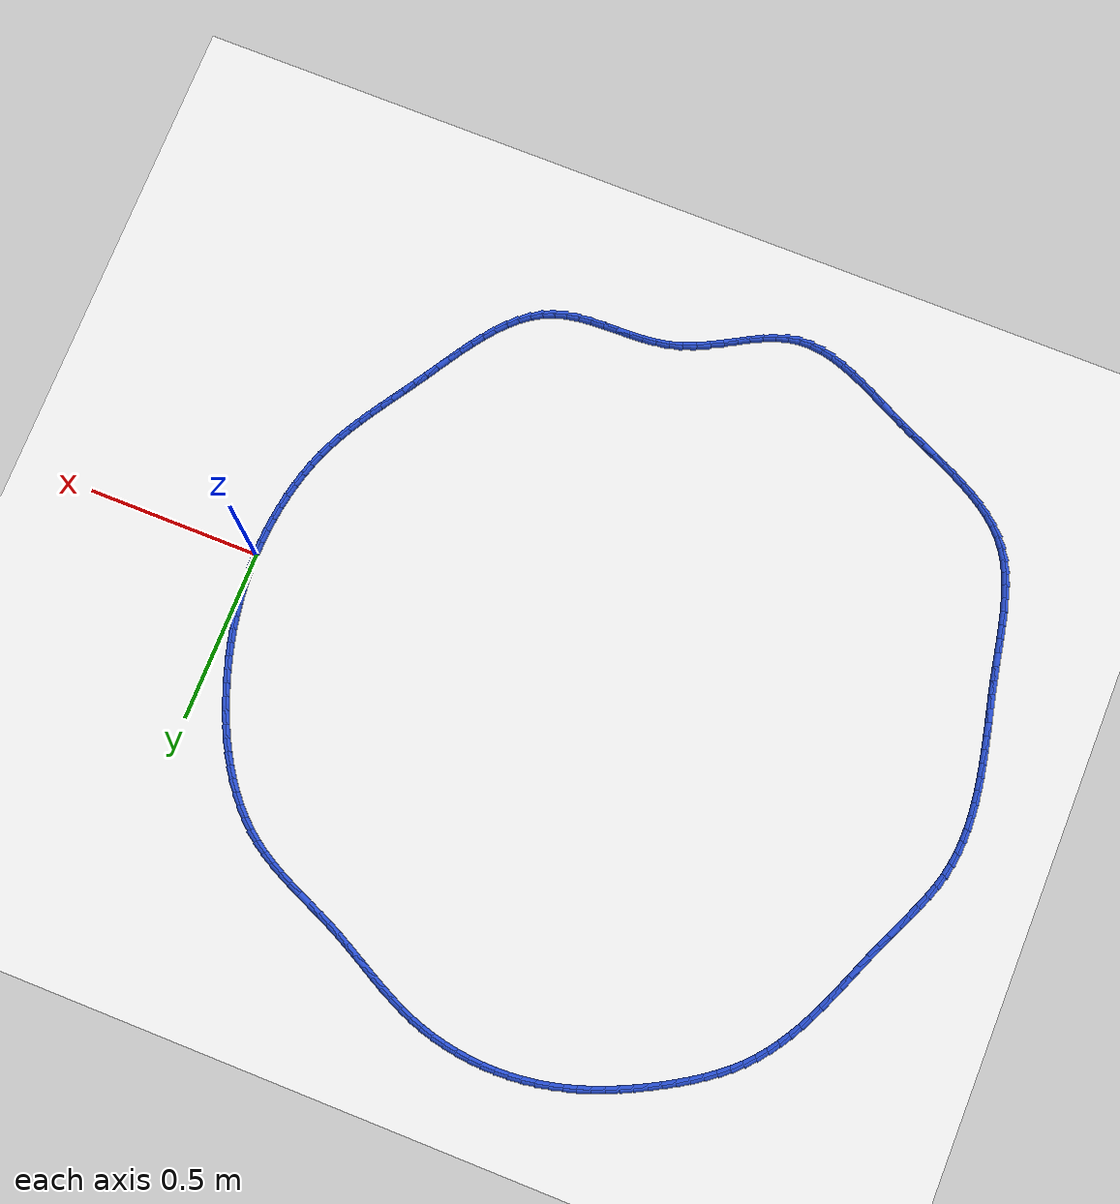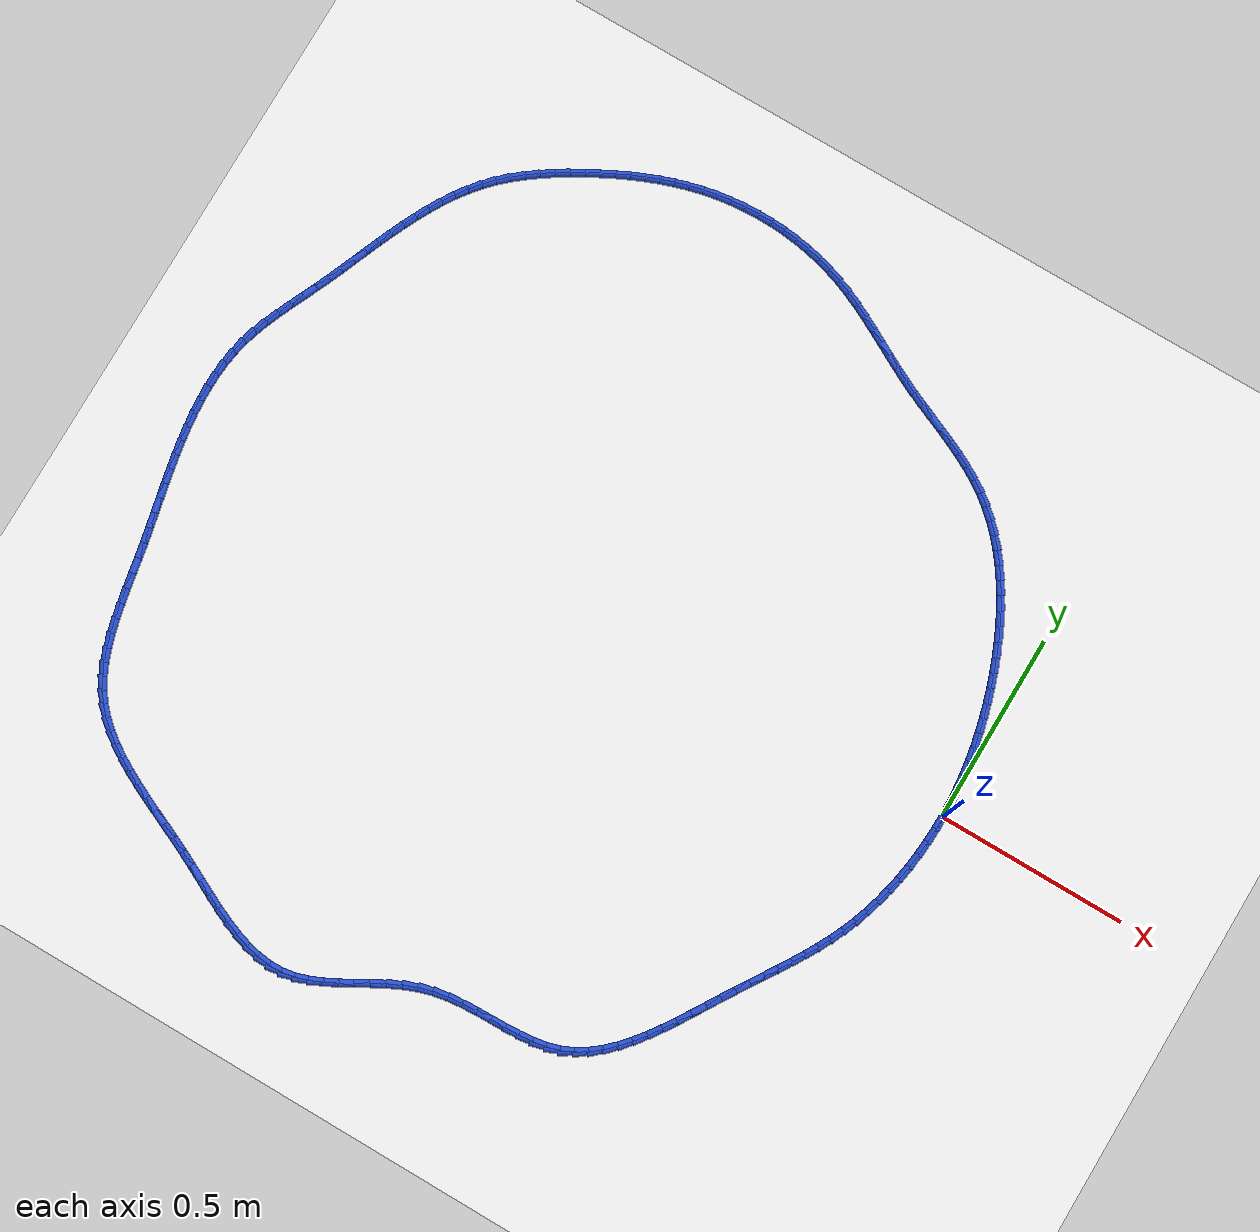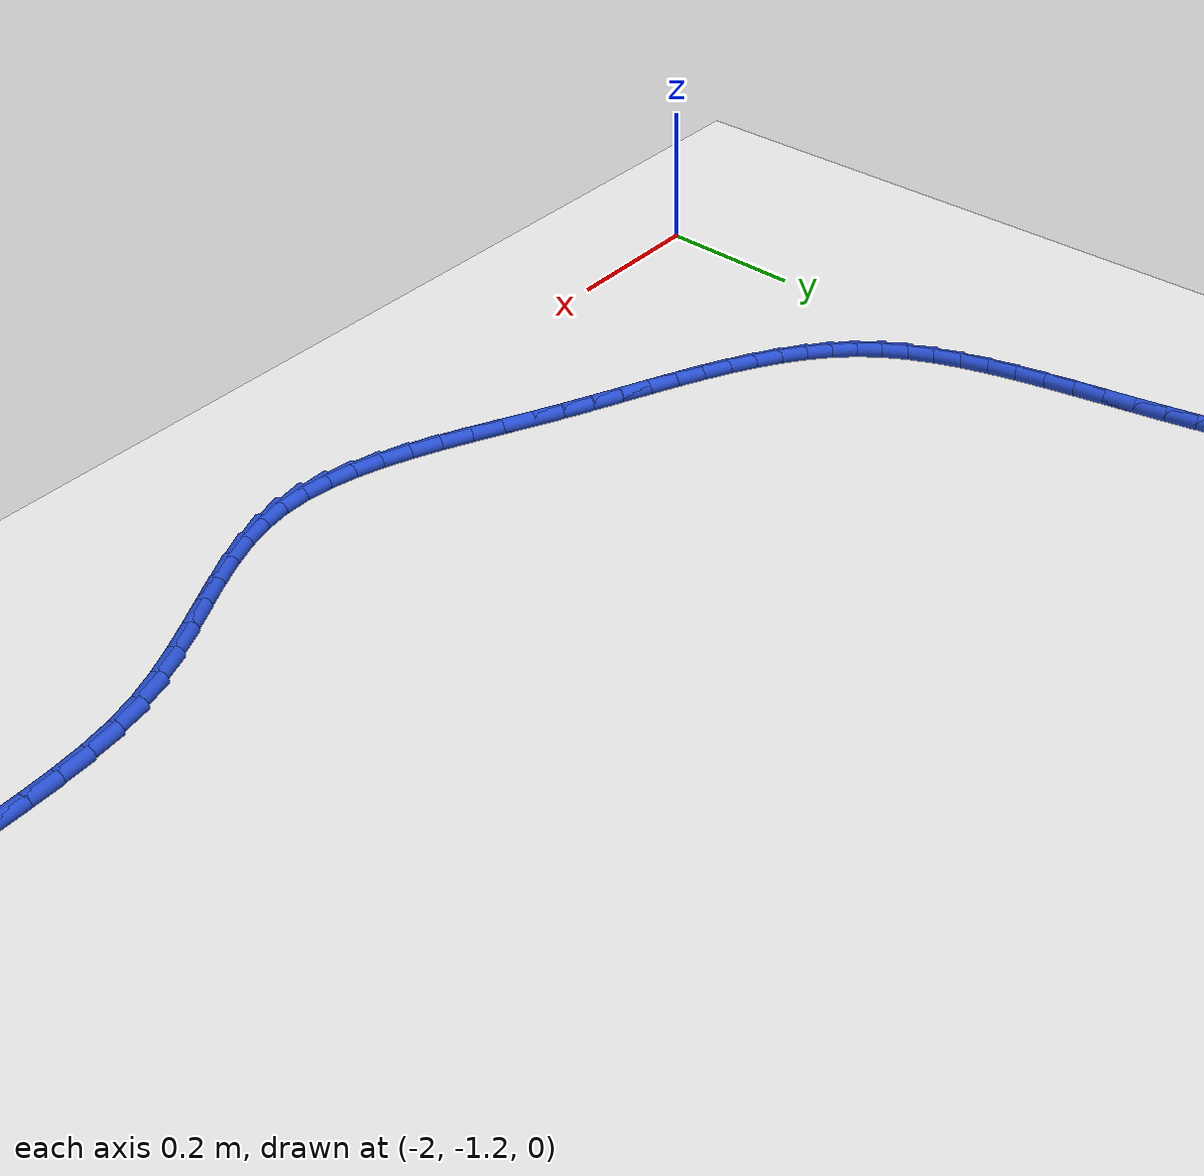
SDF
<sdf version="1.6">
 <world name="default">
  <light name="sun" type="directional">
   <pose>0 0 10 0 -0 0</pose>
   <diffuse>0.8 0.8 0.8 1</diffuse>
   <specular>0.2 0.2 0.2 1</specular>
   <attenuation>
    <range>1000</range>
    <constant>0.9</constant>
    <linear>0.01</linear>
    <quadratic>0.001</quadratic>
   </attenuation>
   <direction>-0.5 0.1 -0.9</direction>
  </light>
  <model name="ground_plane">
   <static>1</static>
   <link name="link">
    <collision name="collision">
     <geometry><plane><normal>0 0 1</normal><size>100 100</size></plane></geometry>
     <surface><friction><ode><mu>100</mu><mu2>50</mu2></ode></friction></surface>
    </collision>
    <visual name="visual">
     <cast_shadows>0</cast_shadows>
     <geometry><plane><normal>0 0 1</normal><size>100 100</size></plane></geometry>
     <material>
      <script><uri>file://media/materials/scripts/gazebo.material</uri><name>Gazebo/WhiteGlow</name></script>
     </material>
    </visual>
   </link>
  </model>
  <gravity>0 0 -9.8</gravity>
  <magnetic_field>6e-06 2.3e-05 -4.2e-05</magnetic_field>
  <atmosphere type="adiabatic"/>
  <physics name="default_physics" default="0" type="ode">
   <max_step_size>0.001</max_step_size>
   <real_time_factor>1</real_time_factor>
   <real_time_update_rate>1000</real_time_update_rate>
  </physics>
  <scene><ambient>0.4 0.4 0.4 1</ambient><background>0.7 0.7 0.7 1</background><shadows>1</shadows></scene>
  <spherical_coordinates>
   <surface_model>EARTH_WGS84</surface_model>
   <latitude_deg>0</latitude_deg>
   <longitude_deg>0</longitude_deg>
   <elevation>0</elevation>
   <heading_deg>0</heading_deg>
  </spherical_coordinates>
  <model name="line">
   <link name="link_0">
    <pose>1.3877787807814457e-17 -1.0408340855860843e-16 0.01 0 1.57 -1.5421332391489484</pose>
    <collision name="collision">
     <geometry><cylinder><radius>0.01</radius><length>0.08</length></cylinder></geometry>
    </collision>
    <visual name="visual">
     <material>
      <script><name>Gazebo/Blue</name><uri>file://media/materials/scripts/gazebo.material</uri></script>
     </material>
     <geometry><cylinder><radius>0.01</radius><length>0.08</length></cylinder></geometry>
    </visual>
   </link>
   <link name="link_1">
    <pose>-0.0010749245003960762 0.037491777626178856 0.01 0 1.57 -1.5053469078658206</pose>
    <collision name="collision">
     <geometry><cylinder><radius>0.01</radius><length>0.08</length></cylinder></geometry>
    </collision>
    <visual name="visual">
     <material>
      <script><name>Gazebo/Blue</name><uri>file://media/materials/scripts/gazebo.material</uri></script>
     </material>
     <geometry><cylinder><radius>0.01</radius><length>0.08</length></cylinder></geometry>
    </visual>
   </link>
   <link name="link_2">
    <pose>-0.003518153114048679 0.07476848734604769 0.01 0 1.57 -1.4690658758729462</pose>
    <collision name="collision">
     <geometry><cylinder><radius>0.01</radius><length>0.08</length></cylinder></geometry>
    </collision>
    <visual name="visual">
     <material>
      <script><name>Gazebo/Blue</name><uri>file://media/materials/scripts/gazebo.material</uri></script>
     </material>
     <geometry><cylinder><radius>0.01</radius><length>0.08</length></cylinder></geometry>
    </visual>
   </link>
   <link name="link_3">
    <pose>-0.007303399781707515 0.11184863069882904 0.01 0 1.57 -1.4334366648536658</pose>
    <collision name="collision">
     <geometry><cylinder><radius>0.01</radius><length>0.08</length></cylinder></geometry>
    </collision>
    <visual name="visual">
     <material>
      <script><name>Gazebo/Blue</name><uri>file://media/materials/scripts/gazebo.material</uri></script>
     </material>
     <geometry><cylinder><radius>0.01</radius><length>0.08</length></cylinder></geometry>
    </visual>
   </link>
   <link name="link_4">
    <pose>-0.012404378444122309 0.14875070922374561 0.01 0 1.57 -1.3985943655154314</pose>
    <collision name="collision">
     <geometry><cylinder><radius>0.01</radius><length>0.08</length></cylinder></geometry>
    </collision>
    <visual name="visual">
     <material>
      <script><name>Gazebo/Blue</name><uri>file://media/materials/scripts/gazebo.material</uri></script>
     </material>
     <geometry><cylinder><radius>0.01</radius><length>0.08</length></cylinder></geometry>
    </visual>
   </link>
   <link name="link_5">
    <pose>-0.018794803042042778 0.18549322446002 0.01 0 1.57 -1.3646605015364055</pose>
    <collision name="collision">
     <geometry><cylinder><radius>0.01</radius><length>0.08</length></cylinder></geometry>
    </collision>
    <visual name="visual">
     <material>
      <script><name>Gazebo/Blue</name><uri>file://media/materials/scripts/gazebo.material</uri></script>
     </material>
     <geometry><cylinder><radius>0.01</radius><length>0.08</length></cylinder></geometry>
    </visual>
   </link>
   <link name="link_6">
    <pose>-0.02644838751621864 0.22209467794687496 0.01 0 1.57 -1.3317415244920079</pose>
    <collision name="collision">
     <geometry><cylinder><radius>0.01</radius><length>0.08</length></cylinder></geometry>
    </collision>
    <visual name="visual">
     <material>
      <script><name>Gazebo/Blue</name><uri>file://media/materials/scripts/gazebo.material</uri></script>
     </material>
     <geometry><cylinder><radius>0.01</radius><length>0.08</length></cylinder></geometry>
    </visual>
   </link>
   <link name="link_7">
    <pose>-0.03533884580739962 0.25857357122353325 0.01 0 1.57 -1.2999279507147503</pose>
    <collision name="collision">
     <geometry><cylinder><radius>0.01</radius><length>0.08</length></cylinder></geometry>
    </collision>
    <visual name="visual">
     <material>
      <script><name>Gazebo/Blue</name><uri>file://media/materials/scripts/gazebo.material</uri></script>
     </material>
     <geometry><cylinder><radius>0.01</radius><length>0.08</length></cylinder></geometry>
    </visual>
   </link>
   <link name="link_8">
    <pose>-0.04543989185633544 0.29494840582921733 0.01 0 1.57 -1.2692941060763583</pose>
    <collision name="collision">
     <geometry><cylinder><radius>0.01</radius><length>0.08</length></cylinder></geometry>
    </collision>
    <visual name="visual">
     <material>
      <script><name>Gazebo/Blue</name><uri>file://media/materials/scripts/gazebo.material</uri></script>
     </material>
     <geometry><cylinder><radius>0.01</radius><length>0.08</length></cylinder></geometry>
    </visual>
   </link>
   <link name="link_9">
    <pose>-0.05672523960377581 0.33123768330314995 0.01 0 1.57 -1.2397175493514214</pose>
    <collision name="collision">
     <geometry><cylinder><radius>0.01</radius><length>0.08</length></cylinder></geometry>
    </collision>
    <visual name="visual">
     <material>
      <script><name>Gazebo/Blue</name><uri>file://media/materials/scripts/gazebo.material</uri></script>
     </material>
     <geometry><cylinder><radius>0.01</radius><length>0.08</length></cylinder></geometry>
    </visual>
   </link>
   <link name="link_10">
    <pose>-0.06917216732138219 0.36744896523237514 0.01 0 1.57 -1.2093169171221858</pose>
    <collision name="collision">
     <geometry><cylinder><radius>0.01</radius><length>0.08</length></cylinder></geometry>
    </collision>
    <visual name="visual">
     <material>
      <script><name>Gazebo/Blue</name><uri>file://media/materials/scripts/gazebo.material</uri></script>
     </material>
     <geometry><cylinder><radius>0.01</radius><length>0.08</length></cylinder></geometry>
    </visual>
   </link>
   <link name="link_11">
    <pose>-0.08279443073317622 0.4034778534576888 0.01 0 1.57 -1.1767810377584496</pose>
    <collision name="collision">
     <geometry><cylinder><radius>0.01</radius><length>0.08</length></cylinder></geometry>
    </collision>
    <visual name="visual">
     <material>
      <script><name>Gazebo/Blue</name><uri>file://media/materials/scripts/gazebo.material</uri></script>
     </material>
     <geometry><cylinder><radius>0.01</radius><length>0.08</length></cylinder></geometry>
    </visual>
   </link>
   <link name="link_12">
    <pose>-0.09762716086988868 0.4391543428829899 0.01 0 1.57 -1.1418173892544796</pose>
    <collision name="collision">
     <geometry><cylinder><radius>0.01</radius><length>0.08</length></cylinder></geometry>
    </collision>
    <visual name="visual">
     <material>
      <script><name>Gazebo/Blue</name><uri>file://media/materials/scripts/gazebo.material</uri></script>
     </material>
     <geometry><cylinder><radius>0.01</radius><length>0.08</length></cylinder></geometry>
    </visual>
   </link>
   <link name="link_13">
    <pose>-0.1137057594886341 0.47430759747538703 0.01 0 1.57 -1.1041287998142197</pose>
    <collision name="collision">
     <geometry><cylinder><radius>0.01</radius><length>0.08</length></cylinder></geometry>
    </collision>
    <visual name="visual">
     <material>
      <script><name>Gazebo/Blue</name><uri>file://media/materials/scripts/gazebo.material</uri></script>
     </material>
     <geometry><cylinder><radius>0.01</radius><length>0.08</length></cylinder></geometry>
    </visual>
   </link>
   <link name="link_14">
    <pose>-0.13106562834652669 0.5087667812019885 0.01 0 1.57 -1.0634009452656619</pose>
    <collision name="collision">
     <geometry><cylinder><radius>0.01</radius><length>0.08</length></cylinder></geometry>
    </collision>
    <visual name="visual">
     <material>
      <script><name>Gazebo/Blue</name><uri>file://media/materials/scripts/gazebo.material</uri></script>
     </material>
     <geometry><cylinder><radius>0.01</radius><length>0.08</length></cylinder></geometry>
    </visual>
   </link>
   <link name="link_15">
    <pose>-0.14974216920068106 0.5423610580299026 0.01 0 1.57 -1.0193063535988565</pose>
    <collision name="collision">
     <geometry><cylinder><radius>0.01</radius><length>0.08</length></cylinder></geometry>
    </collision>
    <visual name="visual">
     <material>
      <script><name>Gazebo/Blue</name><uri>file://media/materials/scripts/gazebo.material</uri></script>
     </material>
     <geometry><cylinder><radius>0.01</radius><length>0.08</length></cylinder></geometry>
    </visual>
   </link>
   <link name="link_16">
    <pose>-0.16977078380821148 0.5749195919262379 0.01 0 1.57 -0.9715122780927599</pose>
    <collision name="collision">
     <geometry><cylinder><radius>0.01</radius><length>0.08</length></cylinder></geometry>
    </collision>
    <visual name="visual">
     <material>
      <script><name>Gazebo/Blue</name><uri>file://media/materials/scripts/gazebo.material</uri></script>
     </material>
     <geometry><cylinder><radius>0.01</radius><length>0.08</length></cylinder></geometry>
    </visual>
   </link>
   <link name="link_17">
    <pose>-0.19118687392623226 0.6062715468581023 0.01 0 1.57 -0.9196937972946188</pose>
    <collision name="collision">
     <geometry><cylinder><radius>0.01</radius><length>0.08</length></cylinder></geometry>
    </collision>
    <visual name="visual">
     <material>
      <script><name>Gazebo/Blue</name><uri>file://media/materials/scripts/gazebo.material</uri></script>
     </material>
     <geometry><cylinder><radius>0.01</radius><length>0.08</length></cylinder></geometry>
    </visual>
   </link>
   <link name="link_18">
    <pose>-0.2140258413118581 0.6362460867926047 0.01 0 1.57 -0.8635536196714912</pose>
    <collision name="collision">
     <geometry><cylinder><radius>0.01</radius><length>0.08</length></cylinder></geometry>
    </collision>
    <visual name="visual">
     <material>
      <script><name>Gazebo/Blue</name><uri>file://media/materials/scripts/gazebo.material</uri></script>
     </material>
     <geometry><cylinder><radius>0.01</radius><length>0.08</length></cylinder></geometry>
    </visual>
   </link>
   <link name="link_19">
    <pose>-0.23832308772220312 0.6646723756968531 0.01 0 1.57 -0.8028498639273242</pose>
    <collision name="collision">
     <geometry><cylinder><radius>0.01</radius><length>0.08</length></cylinder></geometry>
    </collision>
    <visual name="visual">
     <material>
      <script><name>Gazebo/Blue</name><uri>file://media/materials/scripts/gazebo.material</uri></script>
     </material>
     <geometry><cylinder><radius>0.01</radius><length>0.08</length></cylinder></geometry>
    </visual>
   </link>
   <link name="link_20">
    <pose>-0.2641140149143818 0.691379577537956 0.01 0 1.57 -0.7374322756751124</pose>
    <collision name="collision">
     <geometry><cylinder><radius>0.01</radius><length>0.08</length></cylinder></geometry>
    </collision>
    <visual name="visual">
     <material>
      <script><name>Gazebo/Blue</name><uri>file://media/materials/scripts/gazebo.material</uri></script>
     </material>
     <geometry><cylinder><radius>0.01</radius><length>0.08</length></cylinder></geometry>
    </visual>
   </link>
   <link name="link_21">
    <pose>-0.2914340246455086 0.7161968562830217 0.01 0 1.57 -0.6672856169901368</pose>
    <collision name="collision">
     <geometry><cylinder><radius>0.01</radius><length>0.08</length></cylinder></geometry>
    </collision>
    <visual name="visual">
     <material>
      <script><name>Gazebo/Blue</name><uri>file://media/materials/scripts/gazebo.material</uri></script>
     </material>
     <geometry><cylinder><radius>0.01</radius><length>0.08</length></cylinder></geometry>
    </visual>
   </link>
   <link name="link_22">
    <pose>-0.3203185186726979 0.7389533758991584 0.01 0 1.57 -0.5953099155661662</pose>
    <collision name="collision">
     <geometry><cylinder><radius>0.01</radius><length>0.08</length></cylinder></geometry>
    </collision>
    <visual name="visual">
     <material>
      <script><name>Gazebo/Blue</name><uri>file://media/materials/scripts/gazebo.material</uri></script>
     </material>
     <geometry><cylinder><radius>0.01</radius><length>0.08</length></cylinder></geometry>
    </visual>
   </link>
   <link name="link_23">
    <pose>-0.35075547728189393 0.7595675224053315 0.01 0 1.57 -0.5331543355695357</pose>
    <collision name="collision">
     <geometry><cylinder><radius>0.01</radius><length>0.08</length></cylinder></geometry>
    </collision>
    <visual name="visual">
     <material>
      <script><name>Gazebo/Blue</name><uri>file://media/materials/scripts/gazebo.material</uri></script>
     </material>
     <geometry><cylinder><radius>0.01</radius><length>0.08</length></cylinder></geometry>
    </visual>
   </link>
   <link name="link_24">
    <pose>-0.3825379925845536 0.7783243579775551 0.01 0 1.57 -0.4839581522486987</pose>
    <collision name="collision">
     <geometry><cylinder><radius>0.01</radius><length>0.08</length></cylinder></geometry>
    </collision>
    <visual name="visual">
     <material>
      <script><name>Gazebo/Blue</name><uri>file://media/materials/scripts/gazebo.material</uri></script>
     </material>
     <geometry><cylinder><radius>0.01</radius><length>0.08</length></cylinder></geometry>
    </visual>
   </link>
   <link name="link_25">
    <pose>-0.41540909860459974 0.7956031275569844 0.01 0 1.57 -0.4475835850824544</pose>
    <collision name="collision">
     <geometry><cylinder><radius>0.01</radius><length>0.08</length></cylinder></geometry>
    </collision>
    <visual name="visual">
     <material>
      <script><name>Gazebo/Blue</name><uri>file://media/materials/scripts/gazebo.material</uri></script>
     </material>
     <geometry><cylinder><radius>0.01</radius><length>0.08</length></cylinder></geometry>
    </visual>
   </link>
   <link name="link_26">
    <pose>-0.4491118293302137 0.8117830761520202 0.01 0 1.57 -0.4237160033328828</pose>
    <collision name="collision">
     <geometry><cylinder><radius>0.01</radius><length>0.08</length></cylinder></geometry>
    </collision>
    <visual name="visual">
     <material>
      <script><name>Gazebo/Blue</name><uri>file://media/materials/scripts/gazebo.material</uri></script>
     </material>
     <geometry><cylinder><radius>0.01</radius><length>0.08</length></cylinder></geometry>
    </visual>
   </link>
   <link name="link_27">
    <pose>-0.48338921874957724 0.8272434487710636 0.01 0 1.57 -0.41203900918055797</pose>
    <collision name="collision">
     <geometry><cylinder><radius>0.01</radius><length>0.08</length></cylinder></geometry>
    </collision>
    <visual name="visual">
     <material>
      <script><name>Gazebo/Blue</name><uri>file://media/materials/scripts/gazebo.material</uri></script>
     </material>
     <geometry><cylinder><radius>0.01</radius><length>0.08</length></cylinder></geometry>
    </visual>
   </link>
   <link name="link_28">
    <pose>-0.5179843008508721 0.8423634904225151 0.01 0 1.57 -0.41233873418005973</pose>
    <collision name="collision">
     <geometry><cylinder><radius>0.01</radius><length>0.08</length></cylinder></geometry>
    </collision>
    <visual name="visual">
     <material>
      <script><name>Gazebo/Blue</name><uri>file://media/materials/scripts/gazebo.material</uri></script>
     </material>
     <geometry><cylinder><radius>0.01</radius><length>0.08</length></cylinder></geometry>
    </visual>
   </link>
   <link name="link_29">
    <pose>-0.5526401096222798 0.8575224461147751 0.01 0 1.57 -0.4245493605819563</pose>
    <collision name="collision">
     <geometry><cylinder><radius>0.01</radius><length>0.08</length></cylinder></geometry>
    </collision>
    <visual name="visual">
     <material>
      <script><name>Gazebo/Blue</name><uri>file://media/materials/scripts/gazebo.material</uri></script>
     </material>
     <geometry><cylinder><radius>0.01</radius><length>0.08</length></cylinder></geometry>
    </visual>
   </link>
   <link name="link_30">
    <pose>-0.5870996790519818 0.8730995608562446 0.01 0 1.57 -0.44835614252573075</pose>
    <collision name="collision">
     <geometry><cylinder><radius>0.01</radius><length>0.08</length></cylinder></geometry>
    </collision>
    <visual name="visual">
     <material>
      <script><name>Gazebo/Blue</name><uri>file://media/materials/scripts/gazebo.material</uri></script>
     </material>
     <geometry><cylinder><radius>0.01</radius><length>0.08</length></cylinder></geometry>
    </visual>
   </link>
   <link name="link_31">
    <pose>-0.6211136347248953 0.8894612678874579 0.01 0 1.57 -0.47380208929581974</pose>
    <collision name="collision">
     <geometry><cylinder><radius>0.01</radius><length>0.08</length></cylinder></geometry>
    </collision>
    <visual name="visual">
     <material>
      <script><name>Gazebo/Blue</name><uri>file://media/materials/scripts/gazebo.material</uri></script>
     </material>
     <geometry><cylinder><radius>0.01</radius><length>0.08</length></cylinder></geometry>
    </visual>
   </link>
   <link name="link_32">
    <pose>-0.6546271841921648 0.90664561907292 0.01 0 1.57 -0.4901666106193181</pose>
    <collision name="collision">
     <geometry><cylinder><radius>0.01</radius><length>0.08</length></cylinder></geometry>
    </collision>
    <visual name="visual">
     <material>
      <script><name>Gazebo/Blue</name><uri>file://media/materials/scripts/gazebo.material</uri></script>
     </material>
     <geometry><cylinder><radius>0.01</radius><length>0.08</length></cylinder></geometry>
    </visual>
   </link>
   <link name="link_33">
    <pose>-0.6877919071691334 0.9243423874691465 0.01 0 1.57 -0.49687722455286093</pose>
    <collision name="collision">
     <geometry><cylinder><radius>0.01</radius><length>0.08</length></cylinder></geometry>
    </collision>
    <visual name="visual">
     <material>
      <script><name>Gazebo/Blue</name><uri>file://media/materials/scripts/gazebo.material</uri></script>
     </material>
     <geometry><cylinder><radius>0.01</radius><length>0.08</length></cylinder></geometry>
    </visual>
   </link>
   <link name="link_34">
    <pose>-0.7207693355659148 0.9422245505607061 0.01 0 1.57 -0.49387856696736715</pose>
    <collision name="collision">
     <geometry><cylinder><radius>0.01</radius><length>0.08</length></cylinder></geometry>
    </collision>
    <visual name="visual">
     <material>
      <script><name>Gazebo/Blue</name><uri>file://media/materials/scripts/gazebo.material</uri></script>
     </material>
     <geometry><cylinder><radius>0.01</radius><length>0.08</length></cylinder></geometry>
    </visual>
   </link>
   <link name="link_35">
    <pose>-0.7537210012926232 0.9599650858321678 0.01 0 1.57 -0.4810981027536319</pose>
    <collision name="collision">
     <geometry><cylinder><radius>0.01</radius><length>0.08</length></cylinder></geometry>
    </collision>
    <visual name="visual">
     <material>
      <script><name>Gazebo/Blue</name><uri>file://media/materials/scripts/gazebo.material</uri></script>
     </material>
     <geometry><cylinder><radius>0.01</radius><length>0.08</length></cylinder></geometry>
    </visual>
   </link>
   <link name="link_36">
    <pose>-0.7868084362593724 0.9772369707681001 0.01 0 1.57 -0.45845445017022957</pose>
    <collision name="collision">
     <geometry><cylinder><radius>0.01</radius><length>0.08</length></cylinder></geometry>
    </collision>
    <visual name="visual">
     <material>
      <script><name>Gazebo/Blue</name><uri>file://media/materials/scripts/gazebo.material</uri></script>
     </material>
     <geometry><cylinder><radius>0.01</radius><length>0.08</length></cylinder></geometry>
    </visual>
   </link>
   <link name="link_37">
    <pose>-0.8201931723762764 0.9937131828530721 0.01 0 1.57 -0.4258944695536662</pose>
    <collision name="collision">
     <geometry><cylinder><radius>0.01</radius><length>0.08</length></cylinder></geometry>
    </collision>
    <visual name="visual">
     <material>
      <script><name>Gazebo/Blue</name><uri>file://media/materials/scripts/gazebo.material</uri></script>
     </material>
     <geometry><cylinder><radius>0.01</radius><length>0.08</length></cylinder></geometry>
    </visual>
   </link>
   <link name="link_38">
    <pose>-0.8540367415534487 1.0090666995716522 0.01 0 1.57 -0.3834601183704096</pose>
    <collision name="collision">
     <geometry><cylinder><radius>0.01</radius><length>0.08</length></cylinder></geometry>
    </collision>
    <visual name="visual">
     <material>
      <script><name>Gazebo/Blue</name><uri>file://media/materials/scripts/gazebo.material</uri></script>
     </material>
     <geometry><cylinder><radius>0.01</radius><length>0.08</length></cylinder></geometry>
    </visual>
   </link>
   <link name="link_39">
    <pose>-0.8885006757010037 1.0229704984084096 0.01 0 1.57 -0.33152147033300483</pose>
    <collision name="collision">
     <geometry><cylinder><radius>0.01</radius><length>0.08</length></cylinder></geometry>
    </collision>
    <visual name="visual">
     <material>
      <script><name>Gazebo/Blue</name><uri>file://media/materials/scripts/gazebo.material</uri></script>
     </material>
     <geometry><cylinder><radius>0.01</radius><length>0.08</length></cylinder></geometry>
    </visual>
   </link>
   <link name="link_40">
    <pose>-0.9237426920301912 1.0351017071870496 0.01 0 1.57 -0.27522252416295173</pose>
    <collision name="collision">
     <geometry><cylinder><radius>0.01</radius><length>0.08</length></cylinder></geometry>
    </collision>
    <visual name="visual">
     <material>
      <script><name>Gazebo/Blue</name><uri>file://media/materials/scripts/gazebo.material</uri></script>
     </material>
     <geometry><cylinder><radius>0.01</radius><length>0.08</length></cylinder></geometry>
    </visual>
   </link>
   <link name="link_41">
    <pose>-0.9597888168328138 1.0452807316141306 0.01 0 1.57 -0.220350970457594</pose>
    <collision name="collision">
     <geometry><cylinder><radius>0.01</radius><length>0.08</length></cylinder></geometry>
    </collision>
    <visual name="visual">
     <material>
      <script><name>Gazebo/Blue</name><uri>file://media/materials/scripts/gazebo.material</uri></script>
     </material>
     <geometry><cylinder><radius>0.01</radius><length>0.08</length></cylinder></geometry>
    </visual>
   </link>
   <link name="link_42">
    <pose>-0.9965030360026497 1.0535042750882866 0.01 0 1.57 -0.1669655454936474</pose>
    <collision name="collision">
     <geometry><cylinder><radius>0.01</radius><length>0.08</length></cylinder></geometry>
    </collision>
    <visual name="visual">
     <material>
      <script><name>Gazebo/Blue</name><uri>file://media/materials/scripts/gazebo.material</uri></script>
     </material>
     <geometry><cylinder><radius>0.01</radius><length>0.08</length></cylinder></geometry>
    </visual>
   </link>
   <link name="link_43">
    <pose>-1.033739368883642 1.0597798844753046 0.01 0 1.57 -0.11475387068568024</pose>
    <collision name="collision">
     <geometry><cylinder><radius>0.01</radius><length>0.08</length></cylinder></geometry>
    </collision>
    <visual name="visual">
     <material>
      <script><name>Gazebo/Blue</name><uri>file://media/materials/scripts/gazebo.material</uri></script>
     </material>
     <geometry><cylinder><radius>0.01</radius><length>0.08</length></cylinder></geometry>
    </visual>
   </link>
   <link name="link_44">
    <pose>-1.0713518348197342 1.0641151066409722 0.01 0 1.57 -0.06339842151146845</pose>
    <collision name="collision">
     <geometry><cylinder><radius>0.01</radius><length>0.08</length></cylinder></geometry>
    </collision>
    <visual name="visual">
     <material>
      <script><name>Gazebo/Blue</name><uri>file://media/materials/scripts/gazebo.material</uri></script>
     </material>
     <geometry><cylinder><radius>0.01</radius><length>0.08</length></cylinder></geometry>
    </visual>
   </link>
   <link name="link_45">
    <pose>-1.10919445315487 1.066517488451077 0.01 0 1.57 -0.01257852714526064</pose>
    <collision name="collision">
     <geometry><cylinder><radius>0.01</radius><length>0.08</length></cylinder></geometry>
    </collision>
    <visual name="visual">
     <material>
      <script><name>Gazebo/Blue</name><uri>file://media/materials/scripts/gazebo.material</uri></script>
     </material>
     <geometry><cylinder><radius>0.01</radius><length>0.08</length></cylinder></geometry>
    </visual>
   </link>
   <link name="link_46">
    <pose>-1.1471212432329934 1.0669945767714066 0.01 0 1.57 0.038028904285957274</pose>
    <collision name="collision">
     <geometry><cylinder><radius>0.01</radius><length>0.08</length></cylinder></geometry>
    </collision>
    <visual name="visual">
     <material>
      <script><name>Gazebo/Blue</name><uri>file://media/materials/scripts/gazebo.material</uri></script>
     </material>
     <geometry><cylinder><radius>0.01</radius><length>0.08</length></cylinder></geometry>
    </visual>
   </link>
   <link name="link_47">
    <pose>-1.1849862243980473 1.0655539184677487 0.01 0 1.57 0.08874947000964806</pose>
    <collision name="collision">
     <geometry><cylinder><radius>0.01</radius><length>0.08</length></cylinder></geometry>
    </collision>
    <visual name="visual">
     <material>
      <script><name>Gazebo/Blue</name><uri>file://media/materials/scripts/gazebo.material</uri></script>
     </material>
     <geometry><cylinder><radius>0.01</radius><length>0.08</length></cylinder></geometry>
    </visual>
   </link>
   <link name="link_48">
    <pose>-1.2226434159939759 1.0622030604058907 0.01 0 1.57 0.13991173649598637</pose>
    <collision name="collision">
     <geometry><cylinder><radius>0.01</radius><length>0.08</length></cylinder></geometry>
    </collision>
    <visual name="visual">
     <material>
      <script><name>Gazebo/Blue</name><uri>file://media/materials/scripts/gazebo.material</uri></script>
     </material>
     <geometry><cylinder><radius>0.01</radius><length>0.08</length></cylinder></geometry>
    </visual>
   </link>
   <link name="link_49">
    <pose>-1.259946837364723 1.05694954945162 0.01 0 1.57 0.19160862552969146</pose>
    <collision name="collision">
     <geometry><cylinder><radius>0.01</radius><length>0.08</length></cylinder></geometry>
    </collision>
    <visual name="visual">
     <material>
      <script><name>Gazebo/Blue</name><uri>file://media/materials/scripts/gazebo.material</uri></script>
     </material>
     <geometry><cylinder><radius>0.01</radius><length>0.08</length></cylinder></geometry>
    </visual>
   </link>
   <link name="link_50">
    <pose>-1.2967610806865706 1.0498080103893568 0.01 0 1.57 0.2417445357180875</pose>
    <collision name="collision">
     <geometry><cylinder><radius>0.01</radius><length>0.08</length></cylinder></geometry>
    </collision>
    <visual name="visual">
     <material>
      <script><name>Gazebo/Blue</name><uri>file://media/materials/scripts/gazebo.material</uri></script>
     </material>
     <geometry><cylinder><radius>0.01</radius><length>0.08</length></cylinder></geometry>
    </visual>
   </link>
   <link name="link_51">
    <pose>-1.3330509390412166 1.0408601468933316 0.01 0 1.57 0.2888864077812815</pose>
    <collision name="collision">
     <geometry><cylinder><radius>0.01</radius><length>0.08</length></cylinder></geometry>
    </collision>
    <visual name="visual">
     <material>
      <script><name>Gazebo/Blue</name><uri>file://media/materials/scripts/gazebo.material</uri></script>
     </material>
     <geometry><cylinder><radius>0.01</radius><length>0.08</length></cylinder></geometry>
    </visual>
   </link>
   <link name="link_52">
    <pose>-1.3688364829812933 1.0302246678062046 0.01 0 1.57 0.3328424665663333</pose>
    <collision name="collision">
     <geometry><cylinder><radius>0.01</radius><length>0.08</length></cylinder></geometry>
    </collision>
    <visual name="visual">
     <material>
      <script><name>Gazebo/Blue</name><uri>file://media/materials/scripts/gazebo.material</uri></script>
     </material>
     <geometry><cylinder><radius>0.01</radius><length>0.08</length></cylinder></geometry>
    </visual>
   </link>
   <link name="link_53">
    <pose>-1.4041383621164452 1.0180206696168501 0.01 0 1.57 0.37350591709621866</pose>
    <collision name="collision">
     <geometry><cylinder><radius>0.01</radius><length>0.08</length></cylinder></geometry>
    </collision>
    <visual name="visual">
     <material>
      <script><name>Gazebo/Blue</name><uri>file://media/materials/scripts/gazebo.material</uri></script>
     </material>
     <geometry><cylinder><radius>0.01</radius><length>0.08</length></cylinder></geometry>
    </visual>
   </link>
   <link name="link_54">
    <pose>-1.438977226056319 1.0043672488141435 0.01 0 1.57 0.4108300248535458</pose>
    <collision name="collision">
     <geometry><cylinder><radius>0.01</radius><length>0.08</length></cylinder></geometry>
    </collision>
    <visual name="visual">
     <material>
      <script><name>Gazebo/Blue</name><uri>file://media/materials/scripts/gazebo.material</uri></script>
     </material>
     <geometry><cylinder><radius>0.01</radius><length>0.08</length></cylinder></geometry>
    </visual>
   </link>
   <link name="link_55">
    <pose>-1.4733737244105596 0.9893835018869583 0.01 0 1.57 0.4448152300290857</pose>
    <collision name="collision">
     <geometry><cylinder><radius>0.01</radius><length>0.08</length></cylinder></geometry>
    </collision>
    <visual name="visual">
     <material>
      <script><name>Gazebo/Blue</name><uri>file://media/materials/scripts/gazebo.material</uri></script>
     </material>
     <geometry><cylinder><radius>0.01</radius><length>0.08</length></cylinder></geometry>
    </visual>
   </link>
   <link name="link_56">
    <pose>-1.5073485067888133 0.9731885253241701 0.01 0 1.57 0.4754965106915483</pose>
    <collision name="collision">
     <geometry><cylinder><radius>0.01</radius><length>0.08</length></cylinder></geometry>
    </collision>
    <visual name="visual">
     <material>
      <script><name>Gazebo/Blue</name><uri>file://media/materials/scripts/gazebo.material</uri></script>
     </material>
     <geometry><cylinder><radius>0.01</radius><length>0.08</length></cylinder></geometry>
    </visual>
   </link>
   <link name="link_57">
    <pose>-1.5409222228007253 0.955901415614653 0.01 0 1.57 0.5029320900702529</pose>
    <collision name="collision">
     <geometry><cylinder><radius>0.01</radius><length>0.08</length></cylinder></geometry>
    </collision>
    <visual name="visual">
     <material>
      <script><name>Gazebo/Blue</name><uri>file://media/materials/scripts/gazebo.material</uri></script>
     </material>
     <geometry><cylinder><radius>0.01</radius><length>0.08</length></cylinder></geometry>
    </visual>
   </link>
   <link name="link_58">
    <pose>-1.574115514060031 0.9376412626100581 0.01 0 1.57 0.5289835280030678</pose>
    <collision name="collision">
     <geometry><cylinder><radius>0.01</radius><length>0.08</length></cylinder></geometry>
    </collision>
    <visual name="visual">
     <material>
      <script><name>Gazebo/Blue</name><uri>file://media/materials/scripts/gazebo.material</uri></script>
     </material>
     <geometry><cylinder><radius>0.01</radius><length>0.08</length></cylinder></geometry>
    </visual>
   </link>
   <link name="link_59">
    <pose>-1.6068933189064762 0.9184809181435972 0.01 0 1.57 0.5598958145214069</pose>
    <collision name="collision">
     <geometry><cylinder><radius>0.01</radius><length>0.08</length></cylinder></geometry>
    </collision>
    <visual name="visual">
     <material>
      <script><name>Gazebo/Blue</name><uri>file://media/materials/scripts/gazebo.material</uri></script>
     </material>
     <geometry><cylinder><radius>0.01</radius><length>0.08</length></cylinder></geometry>
    </visual>
   </link>
   <link name="link_60">
    <pose>-1.639031690788359 0.8983364450041663 0.01 0 1.57 0.5973067775721952</pose>
    <collision name="collision">
     <geometry><cylinder><radius>0.01</radius><length>0.08</length></cylinder></geometry>
    </collision>
    <visual name="visual">
     <material>
      <script><name>Gazebo/Blue</name><uri>file://media/materials/scripts/gazebo.material</uri></script>
     </material>
     <geometry><cylinder><radius>0.01</radius><length>0.08</length></cylinder></geometry>
    </visual>
   </link>
   <link name="link_61">
    <pose>-1.6702666852549124 0.8770907046360723 0.01 0 1.57 0.6416550732925821</pose>
    <collision name="collision">
     <geometry><cylinder><radius>0.01</radius><length>0.08</length></cylinder></geometry>
    </collision>
    <visual name="visual">
     <material>
      <script><name>Gazebo/Blue</name><uri>file://media/materials/scripts/gazebo.material</uri></script>
     </material>
     <geometry><cylinder><radius>0.01</radius><length>0.08</length></cylinder></geometry>
    </visual>
   </link>
   <link name="link_62">
    <pose>-1.7003343578553713 0.8546265584836225 0.01 0 1.57 0.6934182419998544</pose>
    <collision name="collision">
     <geometry><cylinder><radius>0.01</radius><length>0.08</length></cylinder></geometry>
    </collision>
    <visual name="visual">
     <material>
      <script><name>Gazebo/Blue</name><uri>file://media/materials/scripts/gazebo.material</uri></script>
     </material>
     <geometry><cylinder><radius>0.01</radius><length>0.08</length></cylinder></geometry>
    </visual>
   </link>
   <link name="link_63">
    <pose>-1.7289707641389715 0.8308268679911243 0.01 0 1.57 0.7530525478042834</pose>
    <collision name="collision">
     <geometry><cylinder><radius>0.01</radius><length>0.08</length></cylinder></geometry>
    </collision>
    <visual name="visual">
     <material>
      <script><name>Gazebo/Blue</name><uri>file://media/materials/scripts/gazebo.material</uri></script>
     </material>
     <geometry><cylinder><radius>0.01</radius><length>0.08</length></cylinder></geometry>
    </visual>
   </link>
   <link name="link_64">
    <pose>-1.7559119596549455 0.8055744946028849 0.01 0 1.57 0.8206316478421547</pose>
    <collision name="collision">
     <geometry><cylinder><radius>0.01</radius><length>0.08</length></cylinder></geometry>
    </collision>
    <visual name="visual">
     <material>
      <script><name>Gazebo/Blue</name><uri>file://media/materials/scripts/gazebo.material</uri></script>
     </material>
     <geometry><cylinder><radius>0.01</radius><length>0.08</length></cylinder></geometry>
    </visual>
   </link>
   <link name="link_65">
    <pose>-1.7809029240471146 0.7787573959099351 0.01 0 1.57 0.889353332523554</pose>
    <collision name="collision">
     <geometry><cylinder><radius>0.01</radius><length>0.08</length></cylinder></geometry>
    </collision>
    <visual name="visual">
     <material>
      <script><name>Gazebo/Blue</name><uri>file://media/materials/scripts/gazebo.material</uri></script>
     </material>
     <geometry><cylinder><radius>0.01</radius><length>0.08</length></cylinder></geometry>
    </visual>
   </link>
   <link name="link_66">
    <pose>-1.8039102538249414 0.7503900848701187 0.01 0 1.57 0.9515178400448981</pose>
    <collision name="collision">
     <geometry><cylinder><radius>0.01</radius><length>0.08</length></cylinder></geometry>
    </collision>
    <visual name="visual">
     <material>
      <script><name>Gazebo/Blue</name><uri>file://media/materials/scripts/gazebo.material</uri></script>
     </material>
     <geometry><cylinder><radius>0.01</radius><length>0.08</length></cylinder></geometry>
    </visual>
   </link>
   <link name="link_67">
    <pose>-1.8251316529232637 0.7206190494374367 0.01 0 1.57 1.006303522386353</pose>
    <collision name="collision">
     <geometry><cylinder><radius>0.01</radius><length>0.08</length></cylinder></geometry>
    </collision>
    <visual name="visual">
     <material>
      <script><name>Gazebo/Blue</name><uri>file://media/materials/scripts/gazebo.material</uri></script>
     </material>
     <geometry><cylinder><radius>0.01</radius><length>0.08</length></cylinder></geometry>
    </visual>
   </link>
   <link name="link_68">
    <pose>-1.8447756485297655 0.6895969582359849 0.01 0 1.57 1.0535165966597948</pose>
    <collision name="collision">
     <geometry><cylinder><radius>0.01</radius><length>0.08</length></cylinder></geometry>
    </collision>
    <visual name="visual">
     <material>
      <script><name>Gazebo/Blue</name><uri>file://media/materials/scripts/gazebo.material</uri></script>
     </material>
     <geometry><cylinder><radius>0.01</radius><length>0.08</length></cylinder></geometry>
    </visual>
   </link>
   <link name="link_69">
    <pose>-1.8630507678321324 0.6574764798898589 0.01 0 1.57 1.093175055149425</pose>
    <collision name="collision">
     <geometry><cylinder><radius>0.01</radius><length>0.08</length></cylinder></geometry>
    </collision>
    <visual name="visual">
     <material>
      <script><name>Gazebo/Blue</name><uri>file://media/materials/scripts/gazebo.material</uri></script>
     </material>
     <geometry><cylinder><radius>0.01</radius><length>0.08</length></cylinder></geometry>
    </visual>
   </link>
   <link name="link_70">
    <pose>-1.8801655380180489 0.6244102830231558 0.01 0 1.57 1.1254266521872383</pose>
    <collision name="collision">
     <geometry><cylinder><radius>0.01</radius><length>0.08</length></cylinder></geometry>
    </collision>
    <visual name="visual">
     <material>
      <script><name>Gazebo/Blue</name><uri>file://media/materials/scripts/gazebo.material</uri></script>
     </material>
     <geometry><cylinder><radius>0.01</radius><length>0.08</length></cylinder></geometry>
    </visual>
   </link>
   <link name="link_71">
    <pose>-1.8963284862751995 0.590551036259971 0.01 0 1.57 1.1504805944874679</pose>
    <collision name="collision">
     <geometry><cylinder><radius>0.01</radius><length>0.08</length></cylinder></geometry>
    </collision>
    <visual name="visual">
     <material>
      <script><name>Gazebo/Blue</name><uri>file://media/materials/scripts/gazebo.material</uri></script>
     </material>
     <geometry><cylinder><radius>0.01</radius><length>0.08</length></cylinder></geometry>
    </visual>
   </link>
   <link name="link_72">
    <pose>-1.9117481397912683 0.5560514082244007 0.01 0 1.57 1.168556158449016</pose>
    <collision name="collision">
     <geometry><cylinder><radius>0.01</radius><length>0.08</length></cylinder></geometry>
    </collision>
    <visual name="visual">
     <material>
      <script><name>Gazebo/Blue</name><uri>file://media/materials/scripts/gazebo.material</uri></script>
     </material>
     <geometry><cylinder><radius>0.01</radius><length>0.08</length></cylinder></geometry>
    </visual>
   </link>
   <link name="link_73">
    <pose>-1.92663302575394 0.5210640675405415 0.01 0 1.57 1.1798471913529858</pose>
    <collision name="collision">
     <geometry><cylinder><radius>0.01</radius><length>0.08</length></cylinder></geometry>
    </collision>
    <visual name="visual">
     <material>
      <script><name>Gazebo/Blue</name><uri>file://media/materials/scripts/gazebo.material</uri></script>
     </material>
     <geometry><cylinder><radius>0.01</radius><length>0.08</length></cylinder></geometry>
    </visual>
   </link>
   <link name="link_74">
    <pose>-1.9411916713508999 0.48574168283248836 0.01 0 1.57 1.1844997572481204</pose>
    <collision name="collision">
     <geometry><cylinder><radius>0.01</radius><length>0.08</length></cylinder></geometry>
    </collision>
    <visual name="visual">
     <material>
      <script><name>Gazebo/Blue</name><uri>file://media/materials/scripts/gazebo.material</uri></script>
     </material>
     <geometry><cylinder><radius>0.01</radius><length>0.08</length></cylinder></geometry>
    </visual>
   </link>
   <link name="link_75">
    <pose>-1.9556326037698326 0.45023692272433874 0.01 0 1.57 1.1826001019259422</pose>
    <collision name="collision">
     <geometry><cylinder><radius>0.01</radius><length>0.08</length></cylinder></geometry>
    </collision>
    <visual name="visual">
     <material>
      <script><name>Gazebo/Blue</name><uri>file://media/materials/scripts/gazebo.material</uri></script>
     </material>
     <geometry><cylinder><radius>0.01</radius><length>0.08</length></cylinder></geometry>
    </visual>
   </link>
   <link name="link_76">
    <pose>-1.9701643501984212 0.4147024558401879 0.01 0 1.57 1.1741708307575474</pose>
    <collision name="collision">
     <geometry><cylinder><radius>0.01</radius><length>0.08</length></cylinder></geometry>
    </collision>
    <visual name="visual">
     <material>
      <script><name>Gazebo/Blue</name><uri>file://media/materials/scripts/gazebo.material</uri></script>
     </material>
     <geometry><cylinder><radius>0.01</radius><length>0.08</length></cylinder></geometry>
    </visual>
   </link>
   <link name="link_77">
    <pose>-1.984995437824353 0.37929095080413194 0.01 0 1.57 1.1593084396382058</pose>
    <collision name="collision">
     <geometry><cylinder><radius>0.01</radius><length>0.08</length></cylinder></geometry>
    </collision>
    <visual name="visual">
     <material>
      <script><name>Gazebo/Blue</name><uri>file://media/materials/scripts/gazebo.material</uri></script>
     </material>
     <geometry><cylinder><radius>0.01</radius><length>0.08</length></cylinder></geometry>
    </visual>
   </link>
   <link name="link_78">
    <pose>-2.0003295340367666 0.34415334694937677 0.01 0 1.57 1.1456545798271427</pose>
    <collision name="collision">
     <geometry><cylinder><radius>0.01</radius><length>0.08</length></cylinder></geometry>
    </collision>
    <visual name="visual">
     <material>
      <script><name>Gazebo/Blue</name><uri>file://media/materials/scripts/gazebo.material</uri></script>
     </material>
     <geometry><cylinder><radius>0.01</radius><length>0.08</length></cylinder></geometry>
    </visual>
   </link>
   <link name="link_79">
    <pose>-2.016090890198023 0.3093411573499017 0.01 0 1.57 1.1450006950329576</pose>
    <collision name="collision">
     <geometry><cylinder><radius>0.01</radius><length>0.08</length></cylinder></geometry>
    </collision>
    <visual name="visual">
     <material>
      <script><name>Gazebo/Blue</name><uri>file://media/materials/scripts/gazebo.material</uri></script>
     </material>
     <geometry><cylinder><radius>0.01</radius><length>0.08</length></cylinder></geometry>
    </visual>
   </link>
   <link name="link_80">
    <pose>-2.0317775203473625 0.2747542245292578 0.01 0 1.57 1.1585951568784718</pose>
    <collision name="collision">
     <geometry><cylinder><radius>0.01</radius><length>0.08</length></cylinder></geometry>
    </collision>
    <visual name="visual">
     <material>
      <script><name>Gazebo/Blue</name><uri>file://media/materials/scripts/gazebo.material</uri></script>
     </material>
     <geometry><cylinder><radius>0.01</radius><length>0.08</length></cylinder></geometry>
    </visual>
   </link>
   <link name="link_81">
    <pose>-2.0468515628850925 0.2402796251699766 0.01 0 1.57 1.1869557409004703</pose>
    <collision name="collision">
     <geometry><cylinder><radius>0.01</radius><length>0.08</length></cylinder></geometry>
    </collision>
    <visual name="visual">
     <material>
      <script><name>Gazebo/Blue</name><uri>file://media/materials/scripts/gazebo.material</uri></script>
     </material>
     <geometry><cylinder><radius>0.01</radius><length>0.08</length></cylinder></geometry>
    </visual>
   </link>
   <link name="link_82">
    <pose>-2.0607751562115215 0.2058044359545887 0.01 0 1.57 1.230796765758897</pose>
    <collision name="collision">
     <geometry><cylinder><radius>0.01</radius><length>0.08</length></cylinder></geometry>
    </collision>
    <visual name="visual">
     <material>
      <script><name>Gazebo/Blue</name><uri>file://media/materials/scripts/gazebo.material</uri></script>
     </material>
     <geometry><cylinder><radius>0.01</radius><length>0.08</length></cylinder></geometry>
    </visual>
   </link>
   <link name="link_83">
    <pose>-2.0730104387269557 0.17121573356562453 0.01 0 1.57 1.2908461554128507</pose>
    <collision name="collision">
     <geometry><cylinder><radius>0.01</radius><length>0.08</length></cylinder></geometry>
    </collision>
    <visual name="visual">
     <material>
      <script><name>Gazebo/Blue</name><uri>file://media/materials/scripts/gazebo.material</uri></script>
     </material>
     <geometry><cylinder><radius>0.01</radius><length>0.08</length></cylinder></geometry>
    </visual>
   </link>
   <link name="link_84">
    <pose>-2.083019792975648 0.13640063408996614 0.01 0 1.57 1.362573348284718</pose>
    <collision name="collision">
     <geometry><cylinder><radius>0.01</radius><length>0.08</length></cylinder></geometry>
    </collision>
    <visual name="visual">
     <material>
      <script><name>Gazebo/Blue</name><uri>file://media/materials/scripts/gazebo.material</uri></script>
     </material>
     <geometry><cylinder><radius>0.01</radius><length>0.08</length></cylinder></geometry>
    </visual>
   </link>
   <link name="link_85">
    <pose>-2.0904414050471316 0.10127462795943397 0.01 0 1.57 1.431831067976719</pose>
    <collision name="collision">
     <geometry><cylinder><radius>0.01</radius><length>0.08</length></cylinder></geometry>
    </collision>
    <visual name="visual">
     <material>
      <script><name>Gazebo/Blue</name><uri>file://media/materials/scripts/gazebo.material</uri></script>
     </material>
     <geometry><cylinder><radius>0.01</radius><length>0.08</length></cylinder></geometry>
    </visual>
   </link>
   <link name="link_86">
    <pose>-2.0953987169715877 0.06583152495613336 0.01 0 1.57 1.4954360025242495</pose>
    <collision name="collision">
     <geometry><cylinder><radius>0.01</radius><length>0.08</length></cylinder></geometry>
    </collision>
    <visual name="visual">
     <material>
      <script><name>Gazebo/Blue</name><uri>file://media/materials/scripts/gazebo.material</uri></script>
     </material>
     <geometry><cylinder><radius>0.01</radius><length>0.08</length></cylinder></geometry>
    </visual>
   </link>
   <link name="link_87">
    <pose>-2.098098186201555 0.030078533387354972 0.01 0 1.57 1.5528237257164188</pose>
    <collision name="collision">
     <geometry><cylinder><radius>0.01</radius><length>0.08</length></cylinder></geometry>
    </collision>
    <visual name="visual">
     <material>
      <script><name>Gazebo/Blue</name><uri>file://media/materials/scripts/gazebo.material</uri></script>
     </material>
     <geometry><cylinder><radius>0.01</radius><length>0.08</length></cylinder></geometry>
    </visual>
   </link>
   <link name="link_88">
    <pose>-2.0987462701895714 -0.005977138439610551 0.01 0 1.57 -1.537883700420675</pose>
    <collision name="collision">
     <geometry><cylinder><radius>0.01</radius><length>0.08</length></cylinder></geometry>
    </collision>
    <visual name="visual">
     <material>
      <script><name>Gazebo/Blue</name><uri>file://media/materials/scripts/gazebo.material</uri></script>
     </material>
     <geometry><cylinder><radius>0.01</radius><length>0.08</length></cylinder></geometry>
    </visual>
   </link>
   <link name="link_89">
    <pose>-2.0975494263881744 -0.04232828221747141 0.01 0 1.57 -1.4935659622784996</pose>
    <collision name="collision">
     <geometry><cylinder><radius>0.01</radius><length>0.08</length></cylinder></geometry>
    </collision>
    <visual name="visual">
     <material>
      <script><name>Gazebo/Blue</name><uri>file://media/materials/scripts/gazebo.material</uri></script>
     </material>
     <geometry><cylinder><radius>0.01</radius><length>0.08</length></cylinder></geometry>
    </visual>
   </link>
   <link name="link_90">
    <pose>-2.0947141122499047 -0.07896768963893701 0.01 0 1.57 -1.4557253061426636</pose>
    <collision name="collision">
     <geometry><cylinder><radius>0.01</radius><length>0.08</length></cylinder></geometry>
    </collision>
    <visual name="visual">
     <material>
      <script><name>Gazebo/Blue</name><uri>file://media/materials/scripts/gazebo.material</uri></script>
     </material>
     <geometry><cylinder><radius>0.01</radius><length>0.08</length></cylinder></geometry>
    </visual>
   </link>
   <link name="link_91">
    <pose>-2.0904467852272997 -0.11588815239671629 0.01 0 1.57 -1.4241753916564148</pose>
    <collision name="collision">
     <geometry><cylinder><radius>0.01</radius><length>0.08</length></cylinder></geometry>
    </collision>
    <visual name="visual">
     <material>
      <script><name>Gazebo/Blue</name><uri>file://media/materials/scripts/gazebo.material</uri></script>
     </material>
     <geometry><cylinder><radius>0.01</radius><length>0.08</length></cylinder></geometry>
    </visual>
   </link>
   <link name="link_92">
    <pose>-2.084953902772896 -0.15308246218351898 0.01 0 1.57 -1.3986823940158792</pose>
    <collision name="collision">
     <geometry><cylinder><radius>0.01</radius><length>0.08</length></cylinder></geometry>
    </collision>
    <visual name="visual">
     <material>
      <script><name>Gazebo/Blue</name><uri>file://media/materials/scripts/gazebo.material</uri></script>
     </material>
     <geometry><cylinder><radius>0.01</radius><length>0.08</length></cylinder></geometry>
    </visual>
   </link>
   <link name="link_93">
    <pose>-2.0784419223392354 -0.19054341069205255 0.01 0 1.57 -1.3790011454649973</pose>
    <collision name="collision">
     <geometry><cylinder><radius>0.01</radius><length>0.08</length></cylinder></geometry>
    </collision>
    <visual name="visual">
     <material>
      <script><name>Gazebo/Blue</name><uri>file://media/materials/scripts/gazebo.material</uri></script>
     </material>
     <geometry><cylinder><radius>0.01</radius><length>0.08</length></cylinder></geometry>
    </visual>
   </link>
   <link name="link_94">
    <pose>-2.0711173013788544 -0.22826378961502677 0.01 0 1.57 -1.3649001033048285</pose>
    <collision name="collision">
     <geometry><cylinder><radius>0.01</radius><length>0.08</length></cylinder></geometry>
    </collision>
    <visual name="visual">
     <material>
      <script><name>Gazebo/Blue</name><uri>file://media/materials/scripts/gazebo.material</uri></script>
     </material>
     <geometry><cylinder><radius>0.01</radius><length>0.08</length></cylinder></geometry>
    </visual>
   </link>
   <link name="link_95">
    <pose>-2.0631864973442915 -0.26623639064515053 0.01 0 1.57 -1.3561772295671346</pose>
    <collision name="collision">
     <geometry><cylinder><radius>0.01</radius><length>0.08</length></cylinder></geometry>
    </collision>
    <visual name="visual">
     <material>
      <script><name>Gazebo/Blue</name><uri>file://media/materials/scripts/gazebo.material</uri></script>
     </material>
     <geometry><cylinder><radius>0.01</radius><length>0.08</length></cylinder></geometry>
    </visual>
   </link>
   <link name="link_96">
    <pose>-2.054855967688085 -0.3044540054751329 0.01 0 1.57 -1.3526689261756903</pose>
    <collision name="collision">
     <geometry><cylinder><radius>0.01</radius><length>0.08</length></cylinder></geometry>
    </collision>
    <visual name="visual">
     <material>
      <script><name>Gazebo/Blue</name><uri>file://media/materials/scripts/gazebo.material</uri></script>
     </material>
     <geometry><cylinder><radius>0.01</radius><length>0.08</length></cylinder></geometry>
    </visual>
   </link>
   <link name="link_97">
    <pose>-2.0463321698627746 -0.34290942579768285 0.01 0 1.57 -1.3542537960461738</pose>
    <collision name="collision">
     <geometry><cylinder><radius>0.01</radius><length>0.08</length></cylinder></geometry>
    </collision>
    <visual name="visual">
     <material>
      <script><name>Gazebo/Blue</name><uri>file://media/materials/scripts/gazebo.material</uri></script>
     </material>
     <geometry><cylinder><radius>0.01</radius><length>0.08</length></cylinder></geometry>
    </visual>
   </link>
   <link name="link_98">
    <pose>-2.037821561320898 -0.38159544330551004 0.01 0 1.57 -1.3608524815070073</pose>
    <collision name="collision">
     <geometry><cylinder><radius>0.01</radius><length>0.08</length></cylinder></geometry>
    </collision>
    <visual name="visual">
     <material>
      <script><name>Gazebo/Blue</name><uri>file://media/materials/scripts/gazebo.material</uri></script>
     </material>
     <geometry><cylinder><radius>0.01</radius><length>0.08</length></cylinder></geometry>
    </visual>
   </link>
   <link name="link_99">
    <pose>-2.0295305995149935 -0.42050484969132196 0.01 0 1.57 -1.372188294096108</pose>
    <collision name="collision">
     <geometry><cylinder><radius>0.01</radius><length>0.08</length></cylinder></geometry>
    </collision>
    <visual name="visual">
     <material>
      <script><name>Gazebo/Blue</name><uri>file://media/materials/scripts/gazebo.material</uri></script>
     </material>
     <geometry><cylinder><radius>0.01</radius><length>0.08</length></cylinder></geometry>
    </visual>
   </link>
   <link name="link_100">
    <pose>-2.021656970312106 -0.45962628065893796 0.01 0 1.57 -1.3814006349998413</pose>
    <collision name="collision">
     <geometry><cylinder><radius>0.01</radius><length>0.08</length></cylinder></geometry>
    </collision>
    <visual name="visual">
     <material>
      <script><name>Gazebo/Blue</name><uri>file://media/materials/scripts/gazebo.material</uri></script>
     </material>
     <geometry><cylinder><radius>0.01</radius><length>0.08</length></cylinder></geometry>
    </visual>
   </link>
   <link name="link_101">
    <pose>-2.014142435042089 -0.49882711452556555 0.01 0 1.57 -1.3807596825490325</pose>
    <collision name="collision">
     <geometry><cylinder><radius>0.01</radius><length>0.08</length></cylinder></geometry>
    </collision>
    <visual name="visual">
     <material>
      <script><name>Gazebo/Blue</name><uri>file://media/materials/scripts/gazebo.material</uri></script>
     </material>
     <geometry><cylinder><radius>0.01</radius><length>0.08</length></cylinder></geometry>
    </visual>
   </link>
   <link name="link_102">
    <pose>-2.006638534948726 -0.5378372229450614 0.01 0 1.57 -1.3696857613355655</pose>
    <collision name="collision">
     <geometry><cylinder><radius>0.01</radius><length>0.08</length></cylinder></geometry>
    </collision>
    <visual name="visual">
     <material>
      <script><name>Gazebo/Blue</name><uri>file://media/materials/scripts/gazebo.material</uri></script>
     </material>
     <geometry><cylinder><radius>0.01</radius><length>0.08</length></cylinder></geometry>
    </visual>
   </link>
   <link name="link_103">
    <pose>-1.9987811465578371 -0.5763790556070482 0.01 0 1.57 -1.3476971664473565</pose>
    <collision name="collision">
     <geometry><cylinder><radius>0.01</radius><length>0.08</length></cylinder></geometry>
    </collision>
    <visual name="visual">
     <material>
      <script><name>Gazebo/Blue</name><uri>file://media/materials/scripts/gazebo.material</uri></script>
     </material>
     <geometry><cylinder><radius>0.01</radius><length>0.08</length></cylinder></geometry>
    </visual>
   </link>
   <link name="link_104">
    <pose>-1.990206146395246 -0.6141750622011457 0.01 0 1.57 -1.3139882704953778</pose>
    <collision name="collision">
     <geometry><cylinder><radius>0.01</radius><length>0.08</length></cylinder></geometry>
    </collision>
    <visual name="visual">
     <material>
      <script><name>Gazebo/Blue</name><uri>file://media/materials/scripts/gazebo.material</uri></script>
     </material>
     <geometry><cylinder><radius>0.01</radius><length>0.08</length></cylinder></geometry>
    </visual>
   </link>
   <link name="link_105">
    <pose>-1.9805494109867747 -0.6509476924169767 0.01 0 1.57 -1.2674572673341014</pose>
    <collision name="collision">
     <geometry><cylinder><radius>0.01</radius><length>0.08</length></cylinder></geometry>
    </collision>
    <visual name="visual">
     <material>
      <script><name>Gazebo/Blue</name><uri>file://media/materials/scripts/gazebo.material</uri></script>
     </material>
     <geometry><cylinder><radius>0.01</radius><length>0.08</length></cylinder></geometry>
    </visual>
   </link>
   <link name="link_106">
    <pose>-1.969446816858246 -0.6864193959441629 0.01 0 1.57 -1.2067949294963474</pose>
    <collision name="collision">
     <geometry><cylinder><radius>0.01</radius><length>0.08</length></cylinder></geometry>
    </collision>
    <visual name="visual">
     <material>
      <script><name>Gazebo/Blue</name><uri>file://media/materials/scripts/gazebo.material</uri></script>
     </material>
     <geometry><cylinder><radius>0.01</radius><length>0.08</length></cylinder></geometry>
    </visual>
   </link>
   <link name="link_107">
    <pose>-1.9565342405354802 -0.7203126224723259 0.01 0 1.57 -1.1306892117987464</pose>
    <collision name="collision">
     <geometry><cylinder><radius>0.01</radius><length>0.08</length></cylinder></geometry>
    </collision>
    <visual name="visual">
     <material>
      <script><name>Gazebo/Blue</name><uri>file://media/materials/scripts/gazebo.material</uri></script>
     </material>
     <geometry><cylinder><radius>0.01</radius><length>0.08</length></cylinder></geometry>
    </visual>
   </link>
   <link name="link_108">
    <pose>-1.9414475585443014 -0.7523498216910874 0.01 0 1.57 -1.0382144389401604</pose>
    <collision name="collision">
     <geometry><cylinder><radius>0.01</radius><length>0.08</length></cylinder></geometry>
    </collision>
    <visual name="visual">
     <material>
      <script><name>Gazebo/Blue</name><uri>file://media/materials/scripts/gazebo.material</uri></script>
     </material>
     <geometry><cylinder><radius>0.01</radius><length>0.08</length></cylinder></geometry>
    </visual>
   </link>
   <link name="link_109">
    <pose>-1.9238226474105307 -0.7822534432900698 0.01 0 1.57 -0.9301791211754447</pose>
    <collision name="collision">
     <geometry><cylinder><radius>0.01</radius><length>0.08</length></cylinder></geometry>
    </collision>
    <visual name="visual">
     <material>
      <script><name>Gazebo/Blue</name><uri>file://media/materials/scripts/gazebo.material</uri></script>
     </material>
     <geometry><cylinder><radius>0.01</radius><length>0.08</length></cylinder></geometry>
    </visual>
   </link>
   <link name="link_110">
    <pose>-1.9033144177326398 -0.8097626723370756 0.01 0 1.57 -0.82126412027236</pose>
    <collision name="collision">
     <geometry><cylinder><radius>0.01</radius><length>0.08</length></cylinder></geometry>
    </collision>
    <visual name="visual">
     <material>
      <script><name>Gazebo/Blue</name><uri>file://media/materials/scripts/gazebo.material</uri></script>
     </material>
     <geometry><cylinder><radius>0.01</radius><length>0.08</length></cylinder></geometry>
    </visual>
   </link>
   <link name="link_111">
    <pose>-1.879910189072759 -0.8349089587147207 0.01 0 1.57 -0.7250371680217382</pose>
    <collision name="collision">
     <geometry><cylinder><radius>0.01</radius><length>0.08</length></cylinder></geometry>
    </collision>
    <visual name="visual">
     <material>
      <script><name>Gazebo/Blue</name><uri>file://media/materials/scripts/gazebo.material</uri></script>
     </material>
     <geometry><cylinder><radius>0.01</radius><length>0.08</length></cylinder></geometry>
    </visual>
   </link>
   <link name="link_112">
    <pose>-1.8538799356122424 -0.8579722714762054 0.01 0 1.57 -0.6431682542207866</pose>
    <collision name="collision">
     <geometry><cylinder><radius>0.01</radius><length>0.08</length></cylinder></geometry>
    </collision>
    <visual name="visual">
     <material>
      <script><name>Gazebo/Blue</name><uri>file://media/materials/scripts/gazebo.material</uri></script>
     </material>
     <geometry><cylinder><radius>0.01</radius><length>0.08</length></cylinder></geometry>
    </visual>
   </link>
   <link name="link_113">
    <pose>-1.825502632657568 -0.8792404937578461 0.01 0 1.57 -0.5757173278663115</pose>
    <collision name="collision">
     <geometry><cylinder><radius>0.01</radius><length>0.08</length></cylinder></geometry>
    </collision>
    <visual name="visual">
     <material>
      <script><name>Gazebo/Blue</name><uri>file://media/materials/scripts/gazebo.material</uri></script>
     </material>
     <geometry><cylinder><radius>0.01</radius><length>0.08</length></cylinder></geometry>
    </visual>
   </link>
   <link name="link_114">
    <pose>-1.7950572555152151 -0.8990015086959621 0.01 0 1.57 -0.521994365267637</pose>
    <collision name="collision">
     <geometry><cylinder><radius>0.01</radius><length>0.08</length></cylinder></geometry>
    </collision>
    <visual name="visual">
     <material>
      <script><name>Gazebo/Blue</name><uri>file://media/materials/scripts/gazebo.material</uri></script>
     </material>
     <geometry><cylinder><radius>0.01</radius><length>0.08</length></cylinder></geometry>
    </visual>
   </link>
   <link name="link_115">
    <pose>-1.7628227794916629 -0.9175431994268715 0.01 0 1.57 -0.4809891052238394</pose>
    <collision name="collision">
     <geometry><cylinder><radius>0.01</radius><length>0.08</length></cylinder></geometry>
    </collision>
    <visual name="visual">
     <material>
      <script><name>Gazebo/Blue</name><uri>file://media/materials/scripts/gazebo.material</uri></script>
     </material>
     <geometry><cylinder><radius>0.01</radius><length>0.08</length></cylinder></geometry>
    </visual>
   </link>
   <link name="link_116">
    <pose>-1.729078179893391 -0.9351534490868915 0.01 0 1.57 -0.45165570627455687</pose>
    <collision name="collision">
     <geometry><cylinder><radius>0.01</radius><length>0.08</length></cylinder></geometry>
    </collision>
    <visual name="visual">
     <material>
      <script><name>Gazebo/Blue</name><uri>file://media/materials/scripts/gazebo.material</uri></script>
     </material>
     <geometry><cylinder><radius>0.01</radius><length>0.08</length></cylinder></geometry>
    </visual>
   </link>
   <link name="link_117">
    <pose>-1.6941024320268774 -0.9521201408123406 0.01 0 1.57 -0.43307069379231916</pose>
    <collision name="collision">
     <geometry><cylinder><radius>0.01</radius><length>0.08</length></cylinder></geometry>
    </collision>
    <visual name="visual">
     <material>
      <script><name>Gazebo/Blue</name><uri>file://media/materials/scripts/gazebo.material</uri></script>
     </material>
     <geometry><cylinder><radius>0.01</radius><length>0.08</length></cylinder></geometry>
    </visual>
   </link>
   <link name="link_118">
    <pose>-1.6581745111986017 -0.9687311577395368 0.01 0 1.57 -0.42450498620148597</pose>
    <collision name="collision">
     <geometry><cylinder><radius>0.01</radius><length>0.08</length></cylinder></geometry>
    </collision>
    <visual name="visual">
     <material>
      <script><name>Gazebo/Blue</name><uri>file://media/materials/scripts/gazebo.material</uri></script>
     </material>
     <geometry><cylinder><radius>0.01</radius><length>0.08</length></cylinder></geometry>
    </visual>
   </link>
   <link name="link_119">
    <pose>-1.6215733927150429 -0.9852743830047987 0.01 0 1.57 -0.42544521777746863</pose>
    <collision name="collision">
     <geometry><cylinder><radius>0.01</radius><length>0.08</length></cylinder></geometry>
    </collision>
    <visual name="visual">
     <material>
      <script><name>Gazebo/Blue</name><uri>file://media/materials/scripts/gazebo.material</uri></script>
     </material>
     <geometry><cylinder><radius>0.01</radius><length>0.08</length></cylinder></geometry>
    </visual>
   </link>
   <link name="link_120">
    <pose>-1.5845780518826795 -1.0020376997444442 0.01 0 1.57 -0.43558703518714526</pose>
    <collision name="collision">
     <geometry><cylinder><radius>0.01</radius><length>0.08</length></cylinder></geometry>
    </collision>
    <visual name="visual">
     <material>
      <script><name>Gazebo/Blue</name><uri>file://media/materials/scripts/gazebo.material</uri></script>
     </material>
     <geometry><cylinder><radius>0.01</radius><length>0.08</length></cylinder></geometry>
    </visual>
   </link>
   <link name="link_121">
    <pose>-1.5474674640079915 -1.019308991094791 0.01 0 1.57 -0.45330822308421914</pose>
    <collision name="collision">
     <geometry><cylinder><radius>0.01</radius><length>0.08</length></cylinder></geometry>
    </collision>
    <visual name="visual">
     <material>
      <script><name>Gazebo/Blue</name><uri>file://media/materials/scripts/gazebo.material</uri></script>
     </material>
     <geometry><cylinder><radius>0.01</radius><length>0.08</length></cylinder></geometry>
    </visual>
   </link>
   <link name="link_122">
    <pose>-1.5105032624842292 -1.037315798111702 0.01 0 1.57 -0.46502037150977166</pose>
    <collision name="collision">
     <geometry><cylinder><radius>0.01</radius><length>0.08</length></cylinder></geometry>
    </collision>
    <visual name="visual">
     <material>
      <script><name>Gazebo/Blue</name><uri>file://media/materials/scripts/gazebo.material</uri></script>
     </material>
     <geometry><cylinder><radius>0.01</radius><length>0.08</length></cylinder></geometry>
    </visual>
   </link>
   <link name="link_123">
    <pose>-1.473789090605125 -1.055735927160843 0.01 0 1.57 -0.4635375548807382</pose>
    <collision name="collision">
     <geometry><cylinder><radius>0.01</radius><length>0.08</length></cylinder></geometry>
    </collision>
    <visual name="visual">
     <material>
      <script><name>Gazebo/Blue</name><uri>file://media/materials/scripts/gazebo.material</uri></script>
     </material>
     <geometry><cylinder><radius>0.01</radius><length>0.08</length></cylinder></geometry>
    </visual>
   </link>
   <link name="link_124">
    <pose>-1.437344154676043 -1.0739533817570415 0.01 0 1.57 -0.44843031824717783</pose>
    <collision name="collision">
     <geometry><cylinder><radius>0.01</radius><length>0.08</length></cylinder></geometry>
    </collision>
    <visual name="visual">
     <material>
      <script><name>Gazebo/Blue</name><uri>file://media/materials/scripts/gazebo.material</uri></script>
     </material>
     <geometry><cylinder><radius>0.01</radius><length>0.08</length></cylinder></geometry>
    </visual>
   </link>
   <link name="link_125">
    <pose>-1.4011868655333006 -1.0913493975396003 0.01 0 1.57 -0.4187350550060369</pose>
    <collision name="collision">
     <geometry><cylinder><radius>0.01</radius><length>0.08</length></cylinder></geometry>
    </collision>
    <visual name="visual">
     <material>
      <script><name>Gazebo/Blue</name><uri>file://media/materials/scripts/gazebo.material</uri></script>
     </material>
     <geometry><cylinder><radius>0.01</radius><length>0.08</length></cylinder></geometry>
    </visual>
   </link>
   <link name="link_126">
    <pose>-1.365335634013216 -1.107305210147822 0.01 0 1.57 -0.3728673307870903</pose>
    <collision name="collision">
     <geometry><cylinder><radius>0.01</radius><length>0.08</length></cylinder></geometry>
    </collision>
    <visual name="visual">
     <material>
      <script><name>Gazebo/Blue</name><uri>file://media/materials/scripts/gazebo.material</uri></script>
     </material>
     <geometry><cylinder><radius>0.01</radius><length>0.08</length></cylinder></geometry>
    </visual>
   </link>
   <link name="link_127">
    <pose>-1.3298088709521072 -1.1212020552210091 0.01 0 1.57 -0.308678298807698</pose>
    <collision name="collision">
     <geometry><cylinder><radius>0.01</radius><length>0.08</length></cylinder></geometry>
    </collision>
    <visual name="visual">
     <material>
      <script><name>Gazebo/Blue</name><uri>file://media/materials/scripts/gazebo.material</uri></script>
     </material>
     <geometry><cylinder><radius>0.01</radius><length>0.08</length></cylinder></geometry>
    </visual>
   </link>
   <link name="link_128">
    <pose>-1.2946249871862916 -1.1324211683984644 0.01 0 1.57 -0.22370572086758728</pose>
    <collision name="collision">
     <geometry><cylinder><radius>0.01</radius><length>0.08</length></cylinder></geometry>
    </collision>
    <visual name="visual">
     <material>
      <script><name>Gazebo/Blue</name><uri>file://media/materials/scripts/gazebo.material</uri></script>
     </material>
     <geometry><cylinder><radius>0.01</radius><length>0.08</length></cylinder></geometry>
    </visual>
   </link>
   <link name="link_129">
    <pose>-1.2598023935520872 -1.1403437853194907 0.01 0 1.57 -0.11582707396898931</pose>
    <collision name="collision">
     <geometry><cylinder><radius>0.01</radius><length>0.08</length></cylinder></geometry>
    </collision>
    <visual name="visual">
     <material>
      <script><name>Gazebo/Blue</name><uri>file://media/materials/scripts/gazebo.material</uri></script>
     </material>
     <geometry><cylinder><radius>0.01</radius><length>0.08</length></cylinder></geometry>
    </visual>
   </link>
   <link name="link_130">
    <pose>-1.2253595008858116 -1.1443511416233902 0.01 0 1.57 0.015468646089049418</pose>
    <collision name="collision">
     <geometry><cylinder><radius>0.01</radius><length>0.08</length></cylinder></geometry>
    </collision>
    <visual name="visual">
     <material>
      <script><name>Gazebo/Blue</name><uri>file://media/materials/scripts/gazebo.material</uri></script>
     </material>
     <geometry><cylinder><radius>0.01</radius><length>0.08</length></cylinder></geometry>
    </visual>
   </link>
   <link name="link_131">
    <pose>-1.1913147200237821 -1.1438244729494662 0.01 0 1.57 0.16574984905607065</pose>
    <collision name="collision">
     <geometry><cylinder><radius>0.01</radius><length>0.08</length></cylinder></geometry>
    </collision>
    <visual name="visual">
     <material>
      <script><name>Gazebo/Blue</name><uri>file://media/materials/scripts/gazebo.material</uri></script>
     </material>
     <geometry><cylinder><radius>0.01</radius><length>0.08</length></cylinder></geometry>
    </visual>
   </link>
   <link name="link_132">
    <pose>-1.1576805171731204 -1.1381979887957967 0.01 0 1.57 0.3030118062454791</pose>
    <collision name="collision">
     <geometry><cylinder><radius>0.01</radius><length>0.08</length></cylinder></geometry>
    </collision>
    <visual name="visual">
     <material>
      <script><name>Gazebo/Blue</name><uri>file://media/materials/scripts/gazebo.material</uri></script>
     </material>
     <geometry><cylinder><radius>0.01</radius><length>0.08</length></cylinder></geometry>
    </visual>
   </link>
   <link name="link_133">
    <pose>-1.124370812362249 -1.1277840646789563 0.01 0 1.57 0.4038265379124277</pose>
    <collision name="collision">
     <geometry><cylinder><radius>0.01</radius><length>0.08</length></cylinder></geometry>
    </collision>
    <visual name="visual">
     <material>
      <script><name>Gazebo/Blue</name><uri>file://media/materials/scripts/gazebo.material</uri></script>
     </material>
     <geometry><cylinder><radius>0.01</radius><length>0.08</length></cylinder></geometry>
    </visual>
   </link>
   <link name="link_134">
    <pose>-1.0912184356415795 -1.1136176862062315 0.01 0 1.57 0.4703799302652865</pose>
    <collision name="collision">
     <geometry><cylinder><radius>0.01</radius><length>0.08</length></cylinder></geometry>
    </collision>
    <visual name="visual">
     <material>
      <script><name>Gazebo/Blue</name><uri>file://media/materials/scripts/gazebo.material</uri></script>
     </material>
     <geometry><cylinder><radius>0.01</radius><length>0.08</length></cylinder></geometry>
    </visual>
   </link>
   <link name="link_135">
    <pose>-1.0580538053261042 -1.0967553304736788 0.01 0 1.57 0.5065493199760265</pose>
    <collision name="collision">
     <geometry><cylinder><radius>0.01</radius><length>0.08</length></cylinder></geometry>
    </collision>
    <visual name="visual">
     <material>
      <script><name>Gazebo/Blue</name><uri>file://media/materials/scripts/gazebo.material</uri></script>
     </material>
     <geometry><cylinder><radius>0.01</radius><length>0.08</length></cylinder></geometry>
    </visual>
   </link>
   <link name="link_136">
    <pose>-1.0247073397308137 -1.078253474577354 0.01 0 1.57 0.5153111465258455</pose>
    <collision name="collision">
     <geometry><cylinder><radius>0.01</radius><length>0.08</length></cylinder></geometry>
    </collision>
    <visual name="visual">
     <material>
      <script><name>Gazebo/Blue</name><uri>file://media/materials/scripts/gazebo.material</uri></script>
     </material>
     <geometry><cylinder><radius>0.01</radius><length>0.08</length></cylinder></geometry>
    </visual>
   </link>
   <link name="link_137">
    <pose>-0.9910094571706987 -1.059168595613313 0.01 0 1.57 0.498142785427176</pose>
    <collision name="collision">
     <geometry><cylinder><radius>0.01</radius><length>0.08</length></cylinder></geometry>
    </collision>
    <visual name="visual">
     <material>
      <script><name>Gazebo/Blue</name><uri>file://media/materials/scripts/gazebo.material</uri></script>
     </material>
     <geometry><cylinder><radius>0.01</radius><length>0.08</length></cylinder></geometry>
    </visual>
   </link>
   <link name="link_138">
    <pose>-0.9567905759607516 -1.0405571706776118 0.01 0 1.57 0.45505782785421156</pose>
    <collision name="collision">
     <geometry><cylinder><radius>0.01</radius><length>0.08</length></cylinder></geometry>
    </collision>
    <visual name="visual">
     <material>
      <script><name>Gazebo/Blue</name><uri>file://media/materials/scripts/gazebo.material</uri></script>
     </material>
     <geometry><cylinder><radius>0.01</radius><length>0.08</length></cylinder></geometry>
    </visual>
   </link>
   <link name="link_139">
    <pose>-0.9218811144159632 -1.023475676866307 0.01 0 1.57 0.3850107179537105</pose>
    <collision name="collision">
     <geometry><cylinder><radius>0.01</radius><length>0.08</length></cylinder></geometry>
    </collision>
    <visual name="visual">
     <material>
      <script><name>Gazebo/Blue</name><uri>file://media/materials/scripts/gazebo.material</uri></script>
     </material>
     <geometry><cylinder><radius>0.01</radius><length>0.08</length></cylinder></geometry>
    </visual>
   </link>
   <link name="link_140">
    <pose>-0.8861114908513251 -1.0089805912754544 0.01 0 1.57 0.2875839557276968</pose>
    <collision name="collision">
     <geometry><cylinder><radius>0.01</radius><length>0.08</length></cylinder></geometry>
    </collision>
    <visual name="visual">
     <material>
      <script><name>Gazebo/Blue</name><uri>file://media/materials/scripts/gazebo.material</uri></script>
     </material>
     <geometry><cylinder><radius>0.01</radius><length>0.08</length></cylinder></geometry>
    </visual>
   </link>
   <link name="link_141">
    <pose>-0.8493198227158005 -0.9980982235051202 0.01 0 1.57 0.18659199507845065</pose>
    <collision name="collision">
     <geometry><cylinder><radius>0.01</radius><length>0.08</length></cylinder></geometry>
    </collision>
    <visual name="visual">
     <material>
      <script><name>Gazebo/Blue</name><uri>file://media/materials/scripts/gazebo.material</uri></script>
     </material>
     <geometry><cylinder><radius>0.01</radius><length>0.08</length></cylinder></geometry>
    </visual>
   </link>
   <link name="link_142">
    <pose>-0.8115696913476874 -0.9909714486027235 0.01 0 1.57 0.1097965570118905</pose>
    <collision name="collision">
     <geometry><cylinder><radius>0.01</radius><length>0.08</length></cylinder></geometry>
    </collision>
    <visual name="visual">
     <material>
      <script><name>Gazebo/Blue</name><uri>file://media/materials/scripts/gazebo.material</uri></script>
     </material>
     <geometry><cylinder><radius>0.01</radius><length>0.08</length></cylinder></geometry>
    </visual>
   </link>
   <link name="link_143">
    <pose>-0.7731808295194447 -0.9867394641384793 0.01 0 1.57 0.0581433082539435</pose>
    <collision name="collision">
     <geometry><cylinder><radius>0.01</radius><length>0.08</length></cylinder></geometry>
    </collision>
    <visual name="visual">
     <material>
      <script><name>Gazebo/Blue</name><uri>file://media/materials/scripts/gazebo.material</uri></script>
     </material>
     <geometry><cylinder><radius>0.01</radius><length>0.08</length></cylinder></geometry>
    </visual>
   </link>
   <link name="link_144">
    <pose>-0.7344868379935537 -0.9844871287744995 0.01 0 1.57 0.030710931245391326</pose>
    <collision name="collision">
     <geometry><cylinder><radius>0.01</radius><length>0.08</length></cylinder></geometry>
    </collision>
    <visual name="visual">
     <material>
      <script><name>Gazebo/Blue</name><uri>file://media/materials/scripts/gazebo.material</uri></script>
     </material>
     <geometry><cylinder><radius>0.01</radius><length>0.08</length></cylinder></geometry>
    </visual>
   </link>
   <link name="link_145">
    <pose>-0.695821317532497 -0.9832993011728957 0.01 0 1.57 0.02710478803073976</pose>
    <collision name="collision">
     <geometry><cylinder><radius>0.01</radius><length>0.08</length></cylinder></geometry>
    </collision>
    <visual name="visual">
     <material>
      <script><name>Gazebo/Blue</name><uri>file://media/materials/scripts/gazebo.material</uri></script>
     </material>
     <geometry><cylinder><radius>0.01</radius><length>0.08</length></cylinder></geometry>
    </visual>
   </link>
   <link name="link_146">
    <pose>-0.6575178688987556 -0.982260839995779 0.01 0 1.57 0.047938324825843294</pose>
    <collision name="collision">
     <geometry><cylinder><radius>0.01</radius><length>0.08</length></cylinder></geometry>
    </collision>
    <visual name="visual">
     <material>
      <script><name>Gazebo/Blue</name><uri>file://media/materials/scripts/gazebo.material</uri></script>
     </material>
     <geometry><cylinder><radius>0.01</radius><length>0.08</length></cylinder></geometry>
    </visual>
   </link>
   <link name="link_147">
    <pose>-0.6199100928548121 -0.9804566039052611 0.01 0 1.57 0.09499195022814813</pose>
    <collision name="collision">
     <geometry><cylinder><radius>0.01</radius><length>0.08</length></cylinder></geometry>
    </collision>
    <visual name="visual">
     <material>
      <script><name>Gazebo/Blue</name><uri>file://media/materials/scripts/gazebo.material</uri></script>
     </material>
     <geometry><cylinder><radius>0.01</radius><length>0.08</length></cylinder></geometry>
    </visual>
   </link>
   <link name="link_148">
    <pose>-0.5833315901631476 -0.9769714515634534 0.01 0 1.57 0.1709985525719314</pose>
    <collision name="collision">
     <geometry><cylinder><radius>0.01</radius><length>0.08</length></cylinder></geometry>
    </collision>
    <visual name="visual">
     <material>
      <script><name>Gazebo/Blue</name><uri>file://media/materials/scripts/gazebo.material</uri></script>
     </material>
     <geometry><cylinder><radius>0.01</radius><length>0.08</length></cylinder></geometry>
    </visual>
   </link>
   <link name="link_149">
    <pose>-0.5481159615862456 -0.9708902416324678 0.01 0 1.57 0.27872734426874385</pose>
    <collision name="collision">
     <geometry><cylinder><radius>0.01</radius><length>0.08</length></cylinder></geometry>
    </collision>
    <visual name="visual">
     <material>
      <script><name>Gazebo/Blue</name><uri>file://media/materials/scripts/gazebo.material</uri></script>
     </material>
     <geometry><cylinder><radius>0.01</radius><length>0.08</length></cylinder></geometry>
    </visual>
   </link>
   <link name="link_150">
    <pose>-0.5145968078865872 -0.9612978327744156 0.01 0 1.57 0.4153716893491015</pose>
    <collision name="collision">
     <geometry><cylinder><radius>0.01</radius><length>0.08</length></cylinder></geometry>
    </collision>
    <visual name="visual">
     <material>
      <script><name>Gazebo/Blue</name><uri>file://media/materials/scripts/gazebo.material</uri></script>
     </material>
     <geometry><cylinder><radius>0.01</radius><length>0.08</length></cylinder></geometry>
    </visual>
   </link>
   <link name="link_151">
    <pose>-0.48306538540858057 -0.9473914463990439 0.01 0 1.57 0.5501491001780912</pose>
    <collision name="collision">
     <geometry><cylinder><radius>0.01</radius><length>0.08</length></cylinder></geometry>
    </collision>
    <visual name="visual">
     <material>
      <script><name>Gazebo/Blue</name><uri>file://media/materials/scripts/gazebo.material</uri></script>
     </material>
     <geometry><cylinder><radius>0.01</radius><length>0.08</length></cylinder></geometry>
    </visual>
   </link>
   <link name="link_152">
    <pose>-0.4534816468478527 -0.9292474324995381 0.01 0 1.57 0.6664865368772968</pose>
    <collision name="collision">
     <geometry><cylinder><radius>0.01</radius><length>0.08</length></cylinder></geometry>
    </collision>
    <visual name="visual">
     <material>
      <script><name>Gazebo/Blue</name><uri>file://media/materials/scripts/gazebo.material</uri></script>
     </material>
     <geometry><cylinder><radius>0.01</radius><length>0.08</length></cylinder></geometry>
    </visual>
   </link>
   <link name="link_153">
    <pose>-0.4256495555696082 -0.9073560655145081 0.01 0 1.57 0.7634007361952383</pose>
    <collision name="collision">
     <geometry><cylinder><radius>0.01</radius><length>0.08</length></cylinder></geometry>
    </collision>
    <visual name="visual">
     <material>
      <script><name>Gazebo/Blue</name><uri>file://media/materials/scripts/gazebo.material</uri></script>
     </material>
     <geometry><cylinder><radius>0.01</radius><length>0.08</length></cylinder></geometry>
    </visual>
   </link>
   <link name="link_154">
    <pose>-0.39937216338375975 -0.8822100387340108 0.01 0 1.57 0.8419059101816002</pose>
    <collision name="collision">
     <geometry><cylinder><radius>0.01</radius><length>0.08</length></cylinder></geometry>
    </collision>
    <visual name="visual">
     <material>
      <script><name>Gazebo/Blue</name><uri>file://media/materials/scripts/gazebo.material</uri></script>
     </material>
     <geometry><cylinder><radius>0.01</radius><length>0.08</length></cylinder></geometry>
    </visual>
   </link>
   <link name="link_155">
    <pose>-0.37445252210022184 -0.8543020454481063 0.01 0 1.57 0.9038417432099499</pose>
    <collision name="collision">
     <geometry><cylinder><radius>0.01</radius><length>0.08</length></cylinder></geometry>
    </collision>
    <visual name="visual">
     <material>
      <script><name>Gazebo/Blue</name><uri>file://media/materials/scripts/gazebo.material</uri></script>
     </material>
     <geometry><cylinder><radius>0.01</radius><length>0.08</length></cylinder></geometry>
    </visual>
   </link>
   <link name="link_156">
    <pose>-0.35069368352890734 -0.824124778946853 0.01 0 1.57 0.9511520315326745</pose>
    <collision name="collision">
     <geometry><cylinder><radius>0.01</radius><length>0.08</length></cylinder></geometry>
    </collision>
    <visual name="visual">
     <material>
      <script><name>Gazebo/Blue</name><uri>file://media/materials/scripts/gazebo.material</uri></script>
     </material>
     <geometry><cylinder><radius>0.01</radius><length>0.08</length></cylinder></geometry>
    </visual>
   </link>
   <link name="link_157">
    <pose>-0.3278986994797297 -0.7921709325203093 0.01 0 1.57 0.9855149708142029</pose>
    <collision name="collision">
     <geometry><cylinder><radius>0.01</radius><length>0.08</length></cylinder></geometry>
    </collision>
    <visual name="visual">
     <material>
      <script><name>Gazebo/Blue</name><uri>file://media/materials/scripts/gazebo.material</uri></script>
     </material>
     <geometry><cylinder><radius>0.01</radius><length>0.08</length></cylinder></geometry>
    </visual>
   </link>
   <link name="link_158">
    <pose>-0.3058706217626022 -0.7589331994585341 0.01 0 1.57 1.0081911398608518</pose>
    <collision name="collision">
     <geometry><cylinder><radius>0.01</radius><length>0.08</length></cylinder></geometry>
    </collision>
    <visual name="visual">
     <material>
      <script><name>Gazebo/Blue</name><uri>file://media/materials/scripts/gazebo.material</uri></script>
     </material>
     <geometry><cylinder><radius>0.01</radius><length>0.08</length></cylinder></geometry>
    </visual>
   </link>
   <link name="link_159">
    <pose>-0.28441250218743797 -0.7249042730515854 0.01 0 1.57 1.0199755535001043</pose>
    <collision name="collision">
     <geometry><cylinder><radius>0.01</radius><length>0.08</length></cylinder></geometry>
    </collision>
    <visual name="visual">
     <material>
      <script><name>Gazebo/Blue</name><uri>file://media/materials/scripts/gazebo.material</uri></script>
     </material>
     <geometry><cylinder><radius>0.01</radius><length>0.08</length></cylinder></geometry>
    </visual>
   </link>
   <link name="link_160">
    <pose>-0.2633273925641511 -0.690576846589523 0.01 0 1.57 1.0211842785735548</pose>
    <collision name="collision">
     <geometry><cylinder><radius>0.01</radius><length>0.08</length></cylinder></geometry>
    </collision>
    <visual name="visual">
     <material>
      <script><name>Gazebo/Blue</name><uri>file://media/materials/scripts/gazebo.material</uri></script>
     </material>
     <geometry><cylinder><radius>0.01</radius><length>0.08</length></cylinder></geometry>
    </visual>
   </link>
   <link name="link_161">
    <pose>-0.24241834470265472 -0.6564436133624053 0.01 0 1.57 1.0122568699492733</pose>
    <collision name="collision">
     <geometry><cylinder><radius>0.01</radius><length>0.08</length></cylinder></geometry>
    </collision>
    <visual name="visual">
     <material>
      <script><name>Gazebo/Blue</name><uri>file://media/materials/scripts/gazebo.material</uri></script>
     </material>
     <geometry><cylinder><radius>0.01</radius><length>0.08</length></cylinder></geometry>
    </visual>
   </link>
   <link name="link_162">
    <pose>-0.22150191039477793 -0.6229728608291027 0.01 0 1.57 1.0022374794220605</pose>
    <collision name="collision">
     <geometry><cylinder><radius>0.01</radius><length>0.08</length></cylinder></geometry>
    </collision>
    <visual name="visual">
     <material>
      <script><name>Gazebo/Blue</name><uri>file://media/materials/scripts/gazebo.material</uri></script>
     </material>
     <geometry><cylinder><radius>0.01</radius><length>0.08</length></cylinder></geometry>
    </visual>
   </link>
   <link name="link_163">
    <pose>-0.20060068791107416 -0.5902603770178887 0.01 0 1.57 0.998677699061125</pose>
    <collision name="collision">
     <geometry><cylinder><radius>0.01</radius><length>0.08</length></cylinder></geometry>
    </collision>
    <visual name="visual">
     <material>
      <script><name>Gazebo/Blue</name><uri>file://media/materials/scripts/gazebo.material</uri></script>
     </material>
     <geometry><cylinder><radius>0.01</radius><length>0.08</length></cylinder></geometry>
    </visual>
   </link>
   <link name="link_164">
    <pose>-0.1798979860284388 -0.5581114107909538 0.01 0 1.57 1.002100176411241</pose>
    <collision name="collision">
     <geometry><cylinder><radius>0.01</radius><length>0.08</length></cylinder></geometry>
    </collision>
    <visual name="visual">
     <material>
      <script><name>Gazebo/Blue</name><uri>file://media/materials/scripts/gazebo.material</uri></script>
     </material>
     <geometry><cylinder><radius>0.01</radius><length>0.08</length></cylinder></geometry>
    </visual>
   </link>
   <link name="link_165">
    <pose>-0.15958137043124251 -0.526323515195345 0.01 0 1.57 1.0127731340513297</pose>
    <collision name="collision">
     <geometry><cylinder><radius>0.01</radius><length>0.08</length></cylinder></geometry>
    </collision>
    <visual name="visual">
     <material>
      <script><name>Gazebo/Blue</name><uri>file://media/materials/scripts/gazebo.material</uri></script>
     </material>
     <geometry><cylinder><radius>0.01</radius><length>0.08</length></cylinder></geometry>
    </visual>
   </link>
   <link name="link_166">
    <pose>-0.13983840680385748 -0.49469424327811146 0.01 0 1.57 1.0308902970233402</pose>
    <collision name="collision">
     <geometry><cylinder><radius>0.01</radius><length>0.08</length></cylinder></geometry>
    </collision>
    <visual name="visual">
     <material>
      <script><name>Gazebo/Blue</name><uri>file://media/materials/scripts/gazebo.material</uri></script>
     </material>
     <geometry><cylinder><radius>0.01</radius><length>0.08</length></cylinder></geometry>
    </visual>
   </link>
   <link name="link_167">
    <pose>-0.12085666083065442 -0.46302114808630057 0.01 0 1.57 1.0565449053993972</pose>
    <collision name="collision">
     <geometry><cylinder><radius>0.01</radius><length>0.08</length></cylinder></geometry>
    </collision>
    <visual name="visual">
     <material>
      <script><name>Gazebo/Blue</name><uri>file://media/materials/scripts/gazebo.material</uri></script>
     </material>
     <geometry><cylinder><radius>0.01</radius><length>0.08</length></cylinder></geometry>
    </visual>
   </link>
   <link name="link_168">
    <pose>-0.10282369819600454 -0.43110178266696025 0.01 0 1.57 1.0896924963484211</pose>
    <collision name="collision">
     <geometry><cylinder><radius>0.01</radius><length>0.08</length></cylinder></geometry>
    </collision>
    <visual name="visual">
     <material>
      <script><name>Gazebo/Blue</name><uri>file://media/materials/scripts/gazebo.material</uri></script>
     </material>
     <geometry><cylinder><radius>0.01</radius><length>0.08</length></cylinder></geometry>
    </visual>
   </link>
   <link name="link_169">
    <pose>-0.08592708458427904 -0.39873370006713843 0.01 0 1.57 1.1301053697028893</pose>
    <collision name="collision">
     <geometry><cylinder><radius>0.01</radius><length>0.08</length></cylinder></geometry>
    </collision>
    <visual name="visual">
     <material>
      <script><name>Gazebo/Blue</name><uri>file://media/materials/scripts/gazebo.material</uri></script>
     </material>
     <geometry><cylinder><radius>0.01</radius><length>0.08</length></cylinder></geometry>
    </visual>
   </link>
   <link name="link_170">
    <pose>-0.07035438567984884 -0.36571445333388225 0.01 0 1.57 1.1772868305269282</pose>
    <collision name="collision">
     <geometry><cylinder><radius>0.01</radius><length>0.08</length></cylinder></geometry>
    </collision>
    <visual name="visual">
     <material>
      <script><name>Gazebo/Blue</name><uri>file://media/materials/scripts/gazebo.material</uri></script>
     </material>
     <geometry><cylinder><radius>0.01</radius><length>0.08</length></cylinder></geometry>
    </visual>
   </link>
   <link name="link_171">
    <pose>-0.0562922266355628 -0.3318430642900739 0.01 0 1.57 1.2275779460327185</pose>
    <collision name="collision">
     <geometry><cylinder><radius>0.01</radius><length>0.08</length></cylinder></geometry>
    </collision>
    <visual name="visual">
     <material>
      <script><name>Gazebo/Blue</name><uri>file://media/materials/scripts/gazebo.material</uri></script>
     </material>
     <geometry><cylinder><radius>0.01</radius><length>0.08</length></cylinder></geometry>
    </visual>
   </link>
   <link name="link_172">
    <pose>-0.043852972572768274 -0.2970345225246181 0.01 0 1.57 1.2757165508931723</pose>
    <collision name="collision">
     <geometry><cylinder><radius>0.01</radius><length>0.08</length></cylinder></geometry>
    </collision>
    <visual name="visual">
     <material>
      <script><name>Gazebo/Blue</name><uri>file://media/materials/scripts/gazebo.material</uri></script>
     </material>
     <geometry><cylinder><radius>0.01</radius><length>0.08</length></cylinder></geometry>
    </visual>
   </link>
   <link name="link_173">
    <pose>-0.033022262161670465 -0.26140171928547334 0.01 0 1.57 1.3214772476623793</pose>
    <collision name="collision">
     <geometry><cylinder><radius>0.01</radius><length>0.08</length></cylinder></geometry>
    </collision>
    <visual name="visual">
     <material>
      <script><name>Gazebo/Blue</name><uri>file://media/materials/scripts/gazebo.material</uri></script>
     </material>
     <geometry><cylinder><radius>0.01</radius><length>0.08</length></cylinder></geometry>
    </visual>
   </link>
   <link name="link_174">
    <pose>-0.023773351217370654 -0.22507688343754262 0.01 0 1.57 1.365152655935993</pose>
    <collision name="collision">
     <geometry><cylinder><radius>0.01</radius><length>0.08</length></cylinder></geometry>
    </collision>
    <visual name="visual">
     <material>
      <script><name>Gazebo/Blue</name><uri>file://media/materials/scripts/gazebo.material</uri></script>
     </material>
     <geometry><cylinder><radius>0.01</radius><length>0.08</length></cylinder></geometry>
    </visual>
   </link>
   <link name="link_175">
    <pose>-0.016079495554970086 -0.18819224384572839 0.01 0 1.57 1.4070341408351703</pose>
    <collision name="collision">
     <geometry><cylinder><radius>0.01</radius><length>0.08</length></cylinder></geometry>
    </collision>
    <visual name="visual">
     <material>
      <script><name>Gazebo/Blue</name><uri>file://media/materials/scripts/gazebo.material</uri></script>
     </material>
     <geometry><cylinder><radius>0.01</radius><length>0.08</length></cylinder></geometry>
    </visual>
   </link>
   <link name="link_176">
    <pose>-0.009913950989569922 -0.15088002937493272 0.01 0 1.57 1.4474093043857417</pose>
    <collision name="collision">
     <geometry><cylinder><radius>0.01</radius><length>0.08</length></cylinder></geometry>
    </collision>
    <visual name="visual">
     <material>
      <script><name>Gazebo/Blue</name><uri>file://media/materials/scripts/gazebo.material</uri></script>
     </material>
     <geometry><cylinder><radius>0.01</radius><length>0.08</length></cylinder></geometry>
    </visual>
   </link>
   <link name="link_177">
    <pose>-0.0052499733362716535 -0.11327246889005979 0.01 0 1.57 1.486561447882421</pose>
    <collision name="collision">
     <geometry><cylinder><radius>0.01</radius><length>0.08</length></cylinder></geometry>
    </collision>
    <visual name="visual">
     <material>
      <script><name>Gazebo/Blue</name><uri>file://media/materials/scripts/gazebo.material</uri></script>
     </material>
     <geometry><cylinder><radius>0.01</radius><length>0.08</length></cylinder></geometry>
    </visual>
   </link>
   <link name="link_178">
    <pose>-0.0020608184101764053 -0.07550179125601152 0.01 0 1.57 1.5247705405222018</pose>
    <collision name="collision">
     <geometry><cylinder><radius>0.01</radius><length>0.08</length></cylinder></geometry>
    </collision>
    <visual name="visual">
     <material>
      <script><name>Gazebo/Blue</name><uri>file://media/materials/scripts/gazebo.material</uri></script>
     </material>
     <geometry><cylinder><radius>0.01</radius><length>0.08</length></cylinder></geometry>
    </visual>
   </link>
   <link name="link_179">
    <pose>-0.0003197420263854264 -0.03770022533769068 0.01 0 1.57 1.5623153599710116</pose>
    <collision name="collision">
     <geometry><cylinder><radius>0.01</radius><length>0.08</length></cylinder></geometry>
    </collision>
    <visual name="visual">
     <material>
      <script><name>Gazebo/Blue</name><uri>file://media/materials/scripts/gazebo.material</uri></script>
     </material>
     <geometry><cylinder><radius>0.01</radius><length>0.08</length></cylinder></geometry>
    </visual>
   </link>
   <link name="link_180">
    <pose>2.2551405187698492e-17 9.71445146547012e-17 0.01 0 1.57 -1.5421160670730285</pose>
    <collision name="collision">
     <geometry><cylinder><radius>0.01</radius><length>0.08</length></cylinder></geometry>
    </collision>
    <visual name="visual">
     <material>
      <script><name>Gazebo/Blue</name><uri>file://media/materials/scripts/gazebo.material</uri></script>
     </material>
     <geometry><cylinder><radius>0.01</radius><length>0.08</length></cylinder></geometry>
    </visual>
   </link>
   <link name="link_181">
    <pose>-0.0010748481461213197 0.037466655892158016 0.01 0 1.57 -1.542116067073029</pose>
    <collision name="collision">
     <geometry><cylinder><radius>0.01</radius><length>0.08</length></cylinder></geometry>
    </collision>
    <visual name="visual">
     <material>
      <script><name>Gazebo/Blue</name><uri>file://media/materials/scripts/gazebo.material</uri></script>
     </material>
     <geometry><cylinder><radius>0.01</radius><length>0.08</length></cylinder></geometry>
    </visual>
   </link>
  </model>
 </world>
</sdf>
